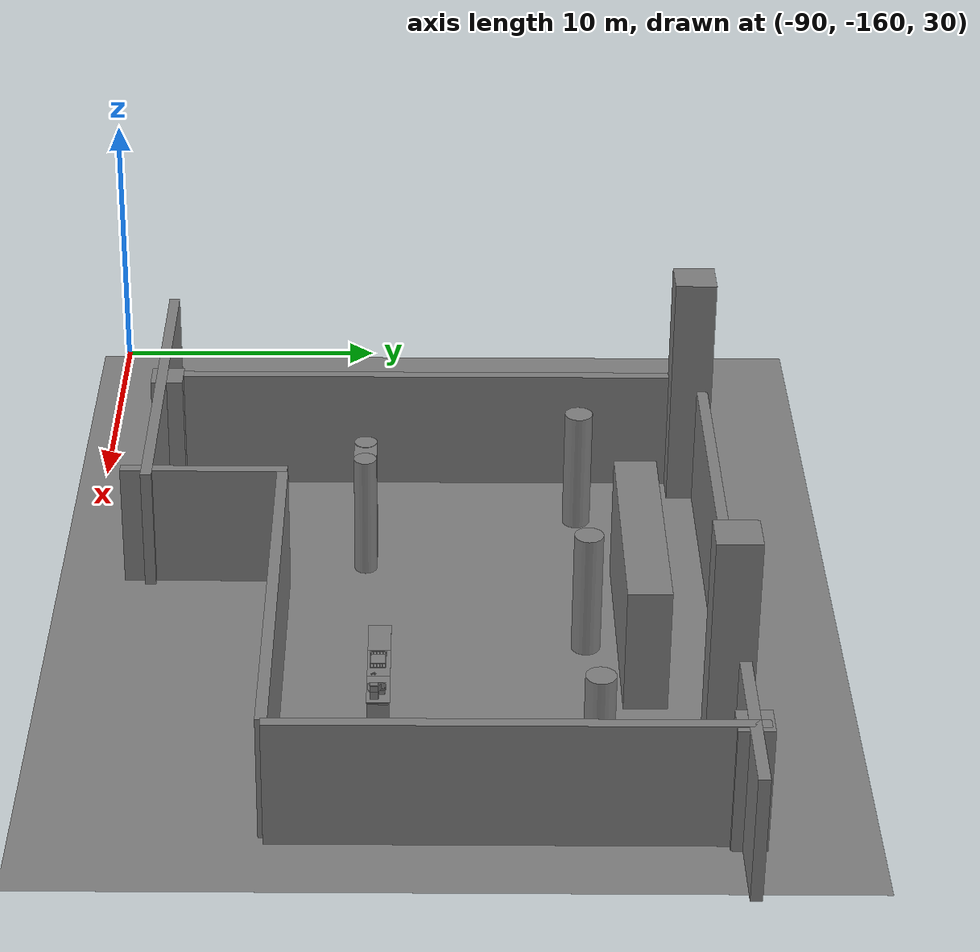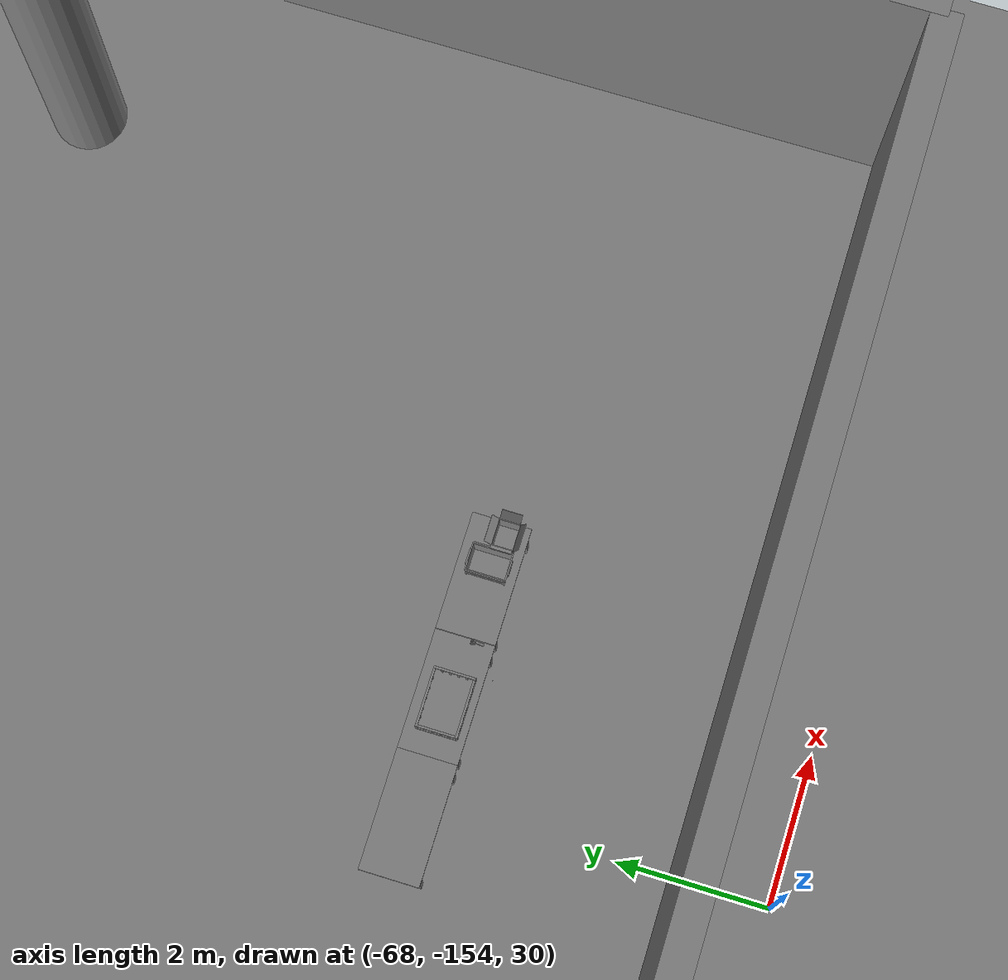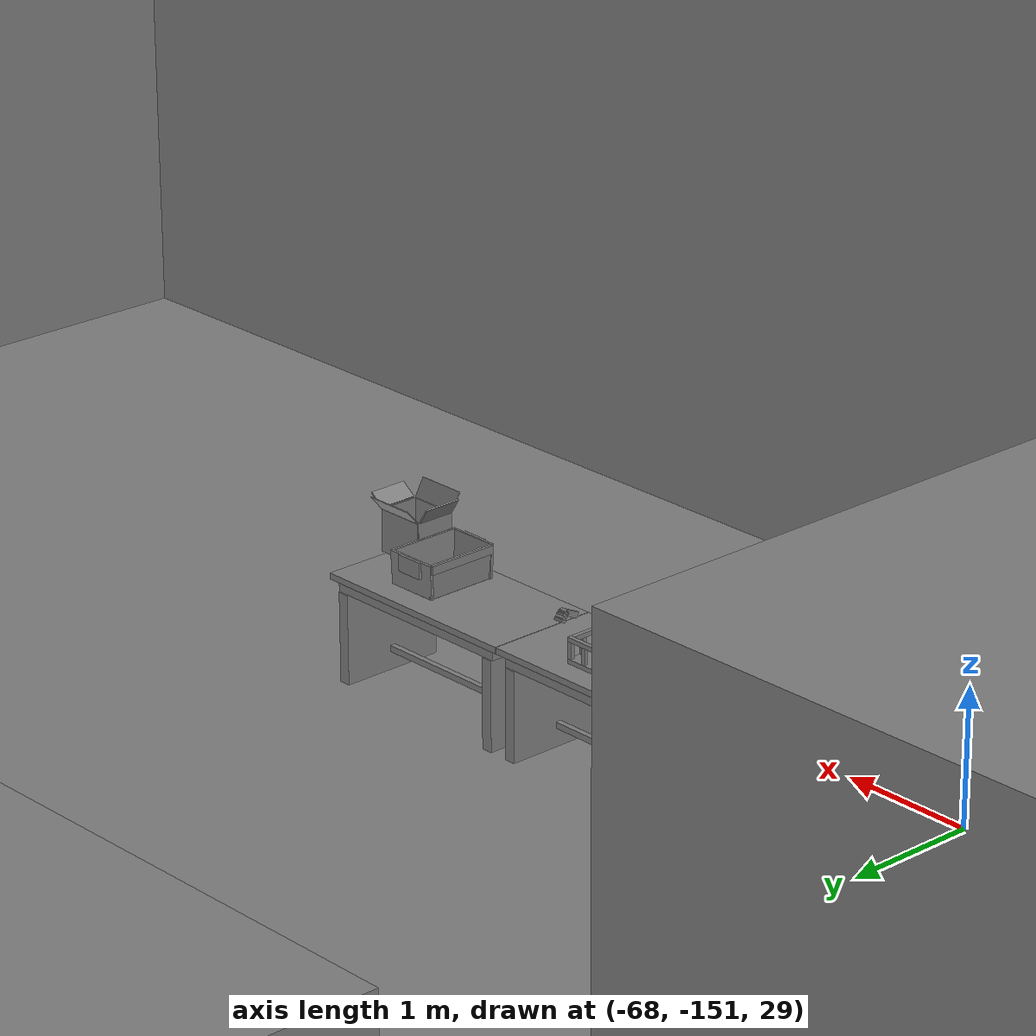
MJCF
<mujoco>
    <option gravity="0.000000000 0.000000000 -9.810000420" timestep="0.0049999999" integrator="implicitfast" density="1.225" viscosity="1.8000001e-05" noslip_iterations="10" iterations="100" sdf_iterations="50">
        <flag multiccd="disable"/>
    </option>
    <size memory="1000M"/>
    <compiler coordinate="local"/>
    <worldbody>
        <light cutoff="30" pos="0 1 1" dir="0 -1 -2"/>
        <light cutoff="30" pos="0 -1 1" dir="0 1 -2"/>
        <body pos="-64.866622925 -149.383972168 30.183746338" euler="89.999992371 89.999946594 0.000000000" name="openloong_gripper_2f85_fix_base_usda_bluebox_01">
            <geom contype="1" conaffinity="1" density="1000" type="box" material="" rgba="0.500000000 0.500000000 0.500000000 1.000000000" solimp="0.899999976 0.949999988 0.001000000" friction="1.000000000 0.005000000 0.000100000" solref="0.020000000 1.000000000" margin="0" condim="3" group="0" pos="0.276596069 0.187225342 0.000061035" quat="0.707107008 0.000077501 0.707106471 0.000077456" size="0.100000001 0.057999998 0.010000000" name="openloong_gripper_2f85_fix_base_usda_geom_0FF9C48A_197B_4F51_9246_1D325A05BD41"/>
            <geom contype="1" conaffinity="1" density="1000" type="box" material="" rgba="0.500000000 0.500000000 0.500000000 1.000000000" solimp="0.899999976 0.949999988 0.001000000" friction="1.000000000 0.005000000 0.000100000" solref="0.020000000 1.000000000" margin="0" condim="3" group="0" pos="0.000000000 0.002883911 0.000000000" quat="1.000000000 0.000000000 0.000000000 0.000000000" size="0.254000008 0.003000000 0.172000006" name="openloong_gripper_2f85_fix_base_usda_geom_E10A5166_1B41_4D81_853F_75695D272DE9"/>
            <geom contype="1" conaffinity="1" density="1000" type="box" material="" rgba="0.500000000 0.500000000 0.500000000 1.000000000" solimp="0.899999976 0.949999988 0.001000000" friction="1.000000000 0.005000000 0.000100000" solref="0.020000000 1.000000000" margin="0" condim="3" group="0" pos="0.000015259 0.124874115 0.173477173" quat="0.999796450 0.020176515 -0.000000015 0.000000030" size="0.259999990 0.119999997 0.007000000" name="openloong_gripper_2f85_fix_base_usda_geom_1E110240_6895_444E_9742_86F06F620DD1"/>
            <geom contype="1" conaffinity="1" density="1000" type="box" material="" rgba="0.500000000 0.500000000 0.500000000 1.000000000" solimp="0.899999976 0.949999988 0.001000000" friction="1.000000000 0.005000000 0.000100000" solref="0.020000000 1.000000000" margin="0" condim="3" group="0" pos="0.000015259 0.124874115 -0.173477173" quat="0.999796450 -0.020176545 -0.000000015 0.000000000" size="0.259999990 0.119999997 0.007000000" name="openloong_gripper_2f85_fix_base_usda_geom_EB683E9D_2320_457C_843A_17A9725569DD"/>
            <geom contype="1" conaffinity="1" density="1000" type="box" material="" rgba="0.500000000 0.500000000 0.500000000 1.000000000" solimp="0.899999976 0.949999988 0.001000000" friction="1.000000000 0.005000000 0.000100000" solref="0.020000000 1.000000000" margin="0" condim="3" group="0" pos="0.000015259 0.214012146 0.188980103" quat="0.999913096 0.013176724 0.000000015 0.000000000" size="0.259999990 0.029999999 0.012500000" name="openloong_gripper_2f85_fix_base_usda_geom_A93989A7_E68A_4455_A4EC_8168EF28E093"/>
            <geom contype="1" conaffinity="1" density="1000" type="box" material="" rgba="0.500000000 0.500000000 0.500000000 1.000000000" solimp="0.899999976 0.949999988 0.001000000" friction="1.000000000 0.005000000 0.000100000" solref="0.020000000 1.000000000" margin="0" condim="3" group="0" pos="-0.258346558 0.125289917 0.001876831" quat="0.702796996 -0.020792052 0.710783184 0.020769238" size="0.189999998 0.119999997 0.009000000" name="openloong_gripper_2f85_fix_base_usda_geom_434673EF_A7D0_48BA_9AAA_2FE13E9F99C3"/>
            <geom contype="1" conaffinity="1" density="1000" type="box" material="" rgba="0.500000000 0.500000000 0.500000000 1.000000000" solimp="0.899999976 0.949999988 0.001000000" friction="1.000000000 0.005000000 0.000100000" solref="0.020000000 1.000000000" margin="0" condim="3" group="0" pos="0.000015259 0.214012146 -0.188980103" quat="0.999913096 -0.013176769 0.000000030 0.000000015" size="0.259999990 0.029999999 0.012500000" name="openloong_gripper_2f85_fix_base_usda_geom_A95DB23E_68C7_4DB4_BF35_110D01929081"/>
            <geom contype="1" conaffinity="1" density="1000" type="box" material="" rgba="0.500000000 0.500000000 0.500000000 1.000000000" solimp="0.899999976 0.949999988 0.001000000" friction="1.000000000 0.005000000 0.000100000" solref="0.020000000 1.000000000" margin="0" condim="3" group="0" pos="-0.276596069 0.187225342 0.000061035" quat="0.707106650 0.000077441 0.707106709 0.000077456" size="0.100000001 0.057999998 0.010000000" name="openloong_gripper_2f85_fix_base_usda_geom_D967C9F9_22BE_4C19_BB2E_602796105679"/>
            <geom contype="1" conaffinity="1" density="1000" type="box" material="" rgba="0.500000000 0.500000000 0.500000000 1.000000000" solimp="0.899999976 0.949999988 0.001000000" friction="1.000000000 0.005000000 0.000100000" solref="0.020000000 1.000000000" margin="0" condim="3" group="0" pos="0.258346558 0.125289917 0.001876831" quat="0.702851534 0.018856451 0.710823834 -0.019329429" size="0.189999998 0.119999997 0.009000000" name="openloong_gripper_2f85_fix_base_usda_geom_22C06281_7915_4F4B_9998_6531D2C3FF37"/>
            <freejoint name="openloong_gripper_2f85_fix_base_usda_bluebox_01_joint"/>
            <site size="0.005000000 0.005000000 0.005000000" rgba="0.500000000 0.500000000 0.500000000 1.000000000" pos="0.000000000 0.000000000 0.000000000" quat="0.999961913 0.008726534 0.000000000 0.000000000" group="0" type="sphere" name="openloong_gripper_2f85_fix_base_usda_bluebox_01site"/>
        </body>
        <body pos="-64.496299744 -149.491867065 30.235729218" euler="0.000000000 0.000000000 89.999946594" name="openloong_gripper_2f85_fix_base_usda_cardboardbox_01">
            <geom contype="1" conaffinity="1" density="1000" type="box" material="" rgba="0.500000000 0.500000000 0.500000000 1.000000000" solimp="0.899999976 0.949999988 0.001000000" friction="1.000000000 0.005000000 0.000100000" solref="0.020000000 1.000000000" margin="0" condim="3" group="0" pos="-0.003166199 -0.004086494 0.005052090" quat="1.000000000 0.000000000 0.000000000 0.000000000" size="0.142499998 0.177500010 0.005000000" name="openloong_gripper_2f85_fix_base_usda_geom_EA7B4EAE_38BF_4119_8CA5_7AAD5D4D4C27"/>
            <geom contype="1" conaffinity="1" density="1000" type="box" material="" rgba="0.500000000 0.500000000 0.500000000 1.000000000" solimp="0.899999976 0.949999988 0.001000000" friction="1.000000000 0.005000000 0.000100000" solref="0.020000000 1.000000000" margin="0" condim="3" group="0" pos="-0.003166199 0.170316696 0.150570869" quat="1.000000000 0.000000000 0.000000000 0.000000000" size="0.142499998 0.005000000 0.149999991" name="openloong_gripper_2f85_fix_base_usda_geom_80D01A20_9DD7_4476_929F_074B0D558EE7"/>
            <geom contype="1" conaffinity="1" density="1000" type="box" material="" rgba="0.500000000 0.500000000 0.500000000 1.000000000" solimp="0.899999976 0.949999988 0.001000000" friction="1.000000000 0.005000000 0.000100000" solref="0.020000000 1.000000000" margin="0" condim="3" group="0" pos="-0.147399902 -0.005307198 0.150570869" quat="1.000000000 0.000000000 0.000000000 0.000000000" size="0.005000000 0.177500010 0.149999991" name="openloong_gripper_2f85_fix_base_usda_geom_9C4311CD_A5DC_414F_A79F_DEC489DCBEE7"/>
            <geom contype="1" conaffinity="1" density="1000" type="box" material="" rgba="0.500000000 0.500000000 0.500000000 1.000000000" solimp="0.899999976 0.949999988 0.001000000" friction="1.000000000 0.005000000 0.000100000" solref="0.020000000 1.000000000" margin="0" condim="3" group="0" pos="0.140275955 -0.005307198 0.150570869" quat="1.000000000 0.000000000 0.000000000 0.000000000" size="0.005000000 0.177500010 0.149999991" name="openloong_gripper_2f85_fix_base_usda_geom_6F74B92A_A441_4DC9_AE5B_F890D417F834"/>
            <geom contype="1" conaffinity="1" density="1000" type="box" material="" rgba="0.500000000 0.500000000 0.500000000 1.000000000" solimp="0.899999976 0.949999988 0.001000000" friction="1.000000000 0.005000000 0.000100000" solref="0.020000000 1.000000000" margin="0" condim="3" group="0" pos="-0.003166199 -0.181550980 0.150570869" quat="1.000000000 0.000000000 0.000000000 0.000000000" size="0.142499998 0.005000000 0.149999991" name="openloong_gripper_2f85_fix_base_usda_geom_C0C2D2C0_4520_4FE6_8B99_81CA9FA468C5"/>
            <freejoint name="openloong_gripper_2f85_fix_base_usda_cardboardbox_01_joint"/>
            <site size="0.005000000 0.005000000 0.005000000" rgba="0.500000000 0.500000000 0.500000000 1.000000000" pos="0.000000000 0.000000000 0.000000000" quat="0.999961913 0.008726535 0.000000000 0.000000000" group="0" type="sphere" name="openloong_gripper_2f85_fix_base_usda_site_58B254DE_56FD_4019_B3A4_A94779CF76C6"/>
            <body pos="0.139160156 -0.004048347 0.301930904" euler="-179.999954224 49.383502960 179.999954224" name="openloong_gripper_2f85_fix_base_usda_A1_006">
                <geom contype="1" conaffinity="1" density="1000" type="box" material="" rgba="0.500000000 0.500000000 0.500000000 1.000000000" solimp="0.899999976 0.949999988 0.001000000" friction="1.000000000 0.005000000 0.000100000" solref="0.020000000 1.000000000" margin="0" condim="3" group="0" pos="-0.071587563 0.000009537 0.001745224" quat="0.999999881 0.000000000 0.000000000 0.000000000" size="0.071249999 0.179999992 0.002500000" name="openloong_gripper_2f85_fix_base_usda_geom_8D095F6E_4BC0_4786_9A67_1818DB9696EB"/>
                <joint armature="0" stiffness="0.07" damping="0.0099999998" axis="0.000000 1.000000 0.000000" type="hinge" name="openloong_gripper_2f85_fix_base_usda_A1_006"/>
            </body>
            <body pos="-0.145902634 -0.004086494 0.301938057" euler="-180.000000000 -60.000011444 -180.000000000" name="openloong_gripper_2f85_fix_base_usda_A2_006">
                <geom contype="1" conaffinity="1" density="1000" type="box" material="" rgba="0.500000000 0.500000000 0.500000000 1.000000000" solimp="0.899999976 0.949999988 0.001000000" friction="1.000000000 0.005000000 0.000100000" solref="0.020000000 1.000000000" margin="0" condim="3" group="0" pos="0.071268082 0.000009537 0.002717972" quat="0.000002921 0.000000000 -0.000000030 0.999999881" size="0.071249999 0.179999992 0.002500000" name="openloong_gripper_2f85_fix_base_usda_geom_D8AC8B4A_54BE_4489_A251_9CB680570854"/>
                <joint armature="0" stiffness="0.07" damping="0.0099999998" axis="0.000000 1.000000 0.000000" type="hinge" name="openloong_gripper_2f85_fix_base_usda_A2_006"/>
            </body>
            <body pos="-0.003385544 0.175991058 0.301930904" euler="-125.858116150 -0.000004561 0.000002331" name="openloong_gripper_2f85_fix_base_usda_B2_006">
                <geom contype="1" conaffinity="1" density="1000" type="box" material="" rgba="0.500000000 0.500000000 0.500000000 1.000000000" solimp="0.899999976 0.949999988 0.001000000" friction="1.000000000 0.005000000 0.000100000" solref="0.020000000 1.000000000" margin="0" condim="3" group="0" pos="0.000009537 -0.070939064 -0.002470016" quat="0.999614120 0.027776197 -0.000000015 0.000000030" size="0.137500003 0.064999998 0.005000000" name="openloong_gripper_2f85_fix_base_usda_geom_395F8845_38F1_4FA2_9CD9_61BDA7A284E7"/>
                <joint armature="0" stiffness="0.07" damping="0.0099999998" axis="1.000000 0.000000 0.000000" type="hinge" name="openloong_gripper_2f85_fix_base_usda_B2_006"/>
            </body>
            <body pos="-0.003385544 -0.184140205 0.301938057" euler="147.805557251 0.000000000 0.000000000" name="openloong_gripper_2f85_fix_base_usda_B1_006">
                <geom contype="1" conaffinity="1" density="1000" type="box" material="" rgba="0.500000000 0.500000000 0.500000000 1.000000000" solimp="0.899999976 0.949999988 0.001000000" friction="1.000000000 0.005000000 0.000100000" solref="0.020000000 1.000000000" margin="0" condim="3" group="0" pos="-0.000028610 0.070202351 -0.002703667" quat="0.999614179 -0.027776167 0.000000000 0.000000000" size="0.137500003 0.064999998 0.005000000" name="openloong_gripper_2f85_fix_base_usda_geom_7361C98C_E011_4422_83BE_BA616A5A1E71"/>
                <joint armature="0" stiffness="0.07" damping="0.0099999998" axis="1.000000 0.000000 0.000000" type="hinge" name="openloong_gripper_2f85_fix_base_usda_B1_006"/>
            </body>
        </body>
        <body pos="-65.882858276 -149.481979370 30.229999542" euler="-64.487716675 0.000000000 0.000000000" name="openloong_gripper_2f85_fix_base_usda_Barcode">
            <geom contype="1" conaffinity="1" density="1000" type="box" material="" rgba="0.500000000 0.500000000 0.500000000 1.000000000" solimp="0.899999976 0.949999988 0.001000000" friction="1.000000000 0.005000000 0.000100000" solref="0.020000000 1.000000000" margin="0" condim="3" group="0" pos="0.000000000 0.013038635 0.001419067" quat="0.000000000 0.000000000 0.000000000 1.000000119" size="0.034000002 0.010000000 0.017999999" name="openloong_gripper_2f85_fix_base_usda_geom_0A297944_E22E_480A_B996_23355AE33A61"/>
            <geom contype="1" conaffinity="1" density="1000" type="box" material="" rgba="0.500000000 0.500000000 0.500000000 1.000000000" solimp="0.899999976 0.949999988 0.001000000" friction="1.000000000 0.005000000 0.000100000" solref="0.020000000 1.000000000" margin="0" condim="3" group="0" pos="0.000000000 -0.035301208 -0.007095337" quat="0.000000000 0.000000000 -0.043619365 0.999048233" size="0.028999999 0.010000000 0.020000000" name="openloong_gripper_2f85_fix_base_usda_geom_104FBE9F_D189_472A_B19B_CC56EB43DF9F"/>
            <geom contype="1" conaffinity="1" density="1000" type="box" material="" rgba="0.500000000 0.500000000 0.500000000 1.000000000" solimp="0.899999976 0.949999988 0.001000000" friction="1.000000000 0.005000000 0.000100000" solref="0.020000000 1.000000000" margin="0" condim="3" group="0" pos="0.000000000 -0.043411255 -0.011749268" quat="0.922262907 0.386563420 0.000000000 0.000000000" size="0.026000001 0.010000000 0.020000000" name="openloong_gripper_2f85_fix_base_usda_geom_725F2189_7C7C_47CF_BAE3_02E53A52FC22"/>
            <geom contype="1" conaffinity="1" density="1000" type="box" material="" rgba="0.500000000 0.500000000 0.500000000 1.000000000" solimp="0.899999976 0.949999988 0.001000000" friction="1.000000000 0.005000000 0.000100000" solref="0.020000000 1.000000000" margin="0" condim="3" group="0" pos="0.000000000 -0.016967773 -0.031860352" quat="0.000000000 0.000000000 0.000000000 1.000000119" size="0.008000000 0.010000000 0.013000000" name="openloong_gripper_2f85_fix_base_usda_geom_146201F4_3DF0_4844_BB53_C3A4F494B52E"/>
            <geom contype="1" conaffinity="1" density="1000" type="box" material="" rgba="0.500000000 0.500000000 0.500000000 1.000000000" solimp="0.899999976 0.949999988 0.001000000" friction="1.000000000 0.005000000 0.000100000" solref="0.020000000 1.000000000" margin="0" condim="3" group="0" pos="0.000000000 -0.001869202 0.000312805" quat="0.953716993 0.300705761 0.000000000 0.000000000" size="0.032000002 0.010000000 0.018999999" name="openloong_gripper_2f85_fix_base_usda_geom_1E1AE2A9_DF13_4F9E_9950_8BA3C0C625A5"/>
            <geom contype="1" conaffinity="1" density="1000" type="box" material="" rgba="0.500000000 0.500000000 0.500000000 1.000000000" solimp="0.899999976 0.949999988 0.001000000" friction="1.000000000 0.005000000 0.000100000" solref="0.020000000 1.000000000" margin="0" condim="3" group="0" pos="0.000000000 -0.019531250 -0.003173828" quat="0.953716993 0.300705761 0.000000000 0.000000000" size="0.030999999 0.010000000 0.020000000" name="openloong_gripper_2f85_fix_base_usda_geom_F75D8745_35BD_45CE_B5C4_7C214CBD5A10"/>
            <geom contype="1" conaffinity="1" density="1000" type="box" material="" rgba="0.500000000 0.500000000 0.500000000 1.000000000" solimp="0.899999976 0.949999988 0.001000000" friction="1.000000000 0.005000000 0.000100000" solref="0.020000000 1.000000000" margin="0" condim="3" group="0" pos="0.000000000 -0.035301208 -0.007095337" quat="0.953716993 0.300705761 0.000000000 0.000000000" size="0.028999999 0.010000000 0.020000000" name="openloong_gripper_2f85_fix_base_usda_geom_C5E8BD34_5123_4A4C_A8BE_D713AC86C3B1"/>
            <geom contype="1" conaffinity="1" density="1000" type="box" material="" rgba="0.500000000 0.500000000 0.500000000 1.000000000" solimp="0.899999976 0.949999988 0.001000000" friction="1.000000000 0.005000000 0.000100000" solref="0.020000000 1.000000000" margin="0" condim="3" group="0" pos="0.000000000 -0.042617798 -0.071121216" quat="0.000000000 0.000000000 0.000000000 1.000000119" size="0.013000000 0.021000000 0.059999999" name="openloong_gripper_2f85_fix_base_usda_geom_D1E18107_4B1A_4EE3_9F29_BC2FA11FBF32"/>
            <freejoint name="openloong_gripper_2f85_fix_base_usda_Barcode_joint"/>
            <site size="0.005000000 0.005000000 0.005000000" rgba="0.500000000 0.500000000 0.500000000 1.000000000" pos="0.000000000 0.000000000 0.000000000" quat="1.000000000 0.000000000 0.000000000 0.000000000" group="0" type="sphere" name="openloong_gripper_2f85_fix_base_usda_Barcode_site"/>
        </body>
        <body pos="-66.745018005 -149.392349243 30.184000015" euler="0.000000000 0.000000000 89.999946594" name="[22331213062734]_Basket_01">
            <geom contype="1" conaffinity="1" density="1000" type="box" material="" rgba="0.500000000 0.500000000 0.500000000 1.000000000" solimp="0.899999976 0.949999988 0.001000000" friction="1.000000000 0.005000000 0.000100000" solref="0.020000000 1.000000000" margin="0" condim="3" group="0" pos="-0.052425385 0.389207840 0.089787483" quat="0.707107008 0.000000000 0.000000000 0.707106411" size="0.014249999 0.014249999 0.059999999" name="[22331213062734]_geom_3B5F9D99_3FC0_425D_8D78_3D427D59542A"/>
            <geom contype="1" conaffinity="1" density="1000" type="box" material="" rgba="0.500000000 0.500000000 0.500000000 1.000000000" solimp="0.899999976 0.949999988 0.001000000" friction="1.000000000 0.005000000 0.000100000" solref="0.020000000 1.000000000" margin="0" condim="3" group="0" pos="0.264015198 -0.133043289 0.089787483" quat="0.707107008 0.000000000 0.000000000 0.707106411" size="0.014249999 0.014249999 0.059999999" name="[22331213062734]_geom_CF5726B0_2867_4A3D_B22D_92BEB14C5605"/>
            <geom contype="1" conaffinity="1" density="1000" type="box" material="" rgba="0.500000000 0.500000000 0.500000000 1.000000000" solimp="0.899999976 0.949999988 0.001000000" friction="1.000000000 0.005000000 0.000100000" solref="0.020000000 1.000000000" margin="0" condim="3" group="0" pos="-0.264015198 -0.265548706 0.089793205" quat="0.707107008 0.000000000 0.000000000 0.707106411" size="0.014249999 0.014249999 0.059999999" name="[22331213062734]_geom_ECAA93A0_AE77_4E09_929C_A2BB9D509742"/>
            <geom contype="1" conaffinity="1" density="1000" type="box" material="" rgba="0.500000000 0.500000000 0.500000000 1.000000000" solimp="0.899999976 0.949999988 0.001000000" friction="1.000000000 0.005000000 0.000100000" solref="0.020000000 1.000000000" margin="0" condim="3" group="0" pos="-0.160263062 -0.389322281 0.089793205" quat="0.707107008 0.000000000 0.000000000 0.707106411" size="0.014249999 0.014249999 0.059999999" name="[22331213062734]_geom_62A8232D_8D8B_4867_AD58_39DF8F65E698"/>
            <geom contype="1" conaffinity="1" density="1000" type="box" material="" rgba="0.500000000 0.500000000 0.500000000 1.000000000" solimp="0.899999976 0.949999988 0.001000000" friction="1.000000000 0.005000000 0.000100000" solref="0.020000000 1.000000000" margin="0" condim="3" group="0" pos="0.162265778 -0.389322281 0.089787483" quat="0.707107008 0.000000000 0.000000000 0.707106411" size="0.014249999 0.014249999 0.059999999" name="[22331213062734]_geom_1560ED24_DD6F_4A2D_B572_23B626578E9F"/>
            <geom contype="1" conaffinity="1" density="1000" type="box" material="" rgba="0.500000000 0.500000000 0.500000000 1.000000000" solimp="0.899999976 0.949999988 0.001000000" friction="1.000000000 0.005000000 0.000100000" solref="0.020000000 1.000000000" margin="0" condim="3" group="0" pos="0.264015198 0.389207840 0.089787483" quat="0.707107008 0.000000000 0.000000000 0.707106411" size="0.014249999 0.014249999 0.059999999" name="[22331213062734]_geom_A59AC13E_F971_485B_86C7_F31D6BD16B56"/>
            <geom contype="1" conaffinity="1" density="1000" type="box" material="" rgba="0.500000000 0.500000000 0.500000000 1.000000000" solimp="0.899999976 0.949999988 0.001000000" friction="1.000000000 0.005000000 0.000100000" solref="0.020000000 1.000000000" margin="0" condim="3" group="0" pos="-0.264015198 -0.133043289 0.089793205" quat="0.707107008 0.000000000 0.000000000 0.707106411" size="0.014249999 0.014249999 0.059999999" name="[22331213062734]_geom_165AB18D_2FDD_4110_B168_93263CFB914A"/>
            <geom contype="1" conaffinity="1" density="1000" type="box" material="" rgba="0.500000000 0.500000000 0.500000000 1.000000000" solimp="0.899999976 0.949999988 0.001000000" friction="1.000000000 0.005000000 0.000100000" solref="0.020000000 1.000000000" margin="0" condim="3" group="0" pos="-0.264026642 0.269256592 0.089793205" quat="0.707107008 0.000000000 0.000000000 0.707106411" size="0.014249999 0.014249999 0.059999999" name="[22331213062734]_geom_97108733_6019_4E31_8506_49132A502613"/>
            <geom contype="1" conaffinity="1" density="1000" type="box" material="" rgba="0.500000000 0.500000000 0.500000000 1.000000000" solimp="0.899999976 0.949999988 0.001000000" friction="1.000000000 0.005000000 0.000100000" solref="0.020000000 1.000000000" margin="0" condim="3" group="0" pos="0.054462433 0.389207840 0.089787483" quat="0.707107008 0.000000000 0.000000000 0.707106411" size="0.014249999 0.014249999 0.059999999" name="[22331213062734]_geom_36E3FDD7_9109_4FB8_8ADC_3E9F19699962"/>
            <geom contype="1" conaffinity="1" density="1000" type="box" material="" rgba="0.500000000 0.500000000 0.500000000 1.000000000" solimp="0.899999976 0.949999988 0.001000000" friction="1.000000000 0.005000000 0.000100000" solref="0.020000000 1.000000000" margin="0" condim="3" group="0" pos="0.054462433 -0.389322281 0.089787483" quat="0.707107008 0.000000000 0.000000000 0.707106411" size="0.014249999 0.014249999 0.059999999" name="[22331213062734]_geom_A67CB686_3DB5_49D6_9017_D72AF4A432F8"/>
            <geom contype="1" conaffinity="1" density="1000" type="box" material="" rgba="0.500000000 0.500000000 0.500000000 1.000000000" solimp="0.899999976 0.949999988 0.001000000" friction="1.000000000 0.005000000 0.000100000" solref="0.020000000 1.000000000" margin="0" condim="3" group="0" pos="0.264015198 0.269256592 0.089793205" quat="0.707107008 0.000000000 0.000000000 0.707106411" size="0.014249999 0.014249999 0.059999999" name="[22331213062734]_geom_4F79A347_6C21_4A08_85C9_7FD59C2D6808"/>
            <geom contype="1" conaffinity="1" density="1000" type="box" material="" rgba="0.500000000 0.500000000 0.500000000 1.000000000" solimp="0.899999976 0.949999988 0.001000000" friction="1.000000000 0.005000000 0.000100000" solref="0.020000000 1.000000000" margin="0" condim="3" group="0" pos="0.264015198 -0.389322281 0.089787483" quat="0.707107008 0.000000000 0.000000000 0.707106411" size="0.014249999 0.014249999 0.059999999" name="[22331213062734]_geom_532FFC08_BE36_422D_814C_6D0D802AE979"/>
            <geom contype="1" conaffinity="1" density="1000" type="box" material="" rgba="0.500000000 0.500000000 0.500000000 1.000000000" solimp="0.899999976 0.949999988 0.001000000" friction="1.000000000 0.005000000 0.000100000" solref="0.020000000 1.000000000" margin="0" condim="3" group="0" pos="0.000000000 0.000000000 0.015998840" quat="0.707107008 0.000000000 0.000000000 0.707106411" size="0.403499991 0.279000014 0.015750000" name="[22331213062734]_geom_8B8A8CD9_B8D7_48CA_A5DF_FF83542267DD"/>
            <geom contype="1" conaffinity="1" density="1000" type="box" material="" rgba="0.500000000 0.500000000 0.500000000 1.000000000" solimp="0.899999976 0.949999988 0.001000000" friction="1.000000000 0.005000000 0.000100000" solref="0.020000000 1.000000000" margin="0" condim="3" group="0" pos="0.000000000 -0.389476776 0.163619041" quat="0.707107008 0.000000000 0.000000000 0.707106411" size="0.015000000 0.277500004 0.015750000" name="[22331213062734]_geom_30FDFC8E_99D2_4630_AC9B_6B88DE451C21"/>
            <geom contype="1" conaffinity="1" density="1000" type="box" material="" rgba="0.500000000 0.500000000 0.500000000 1.000000000" solimp="0.899999976 0.949999988 0.001000000" friction="1.000000000 0.005000000 0.000100000" solref="0.020000000 1.000000000" margin="0" condim="3" group="0" pos="0.162265778 0.389207840 0.089787483" quat="0.707107008 0.000000000 0.000000000 0.707106411" size="0.014249999 0.014249999 0.059999999" name="[22331213062734]_geom_F23FA48B_9724_4E2D_95D5_8DC58C0469EF"/>
            <geom contype="1" conaffinity="1" density="1000" type="box" material="" rgba="0.500000000 0.500000000 0.500000000 1.000000000" solimp="0.899999976 0.949999988 0.001000000" friction="1.000000000 0.005000000 0.000100000" solref="0.020000000 1.000000000" margin="0" condim="3" group="0" pos="0.000000000 0.389471054 0.163619041" quat="0.707107008 0.000000000 0.000000000 0.707106411" size="0.015000000 0.277500004 0.015750000" name="[22331213062734]_geom_9B52D01C_D876_4B8D_8E65_D3873247FBC9"/>
            <geom contype="1" conaffinity="1" density="1000" type="box" material="" rgba="0.500000000 0.500000000 0.500000000 1.000000000" solimp="0.899999976 0.949999988 0.001000000" friction="1.000000000 0.005000000 0.000100000" solref="0.020000000 1.000000000" margin="0" condim="3" group="0" pos="-0.263511658 0.000000000 0.163619041" quat="0.707107008 0.000000000 0.000000000 0.707106411" size="0.403499991 0.015000000 0.015750000" name="[22331213062734]_geom_53BC78EE_D6D6_4F68_91AD_BA5178AD89DC"/>
            <geom contype="1" conaffinity="1" density="1000" type="box" material="" rgba="0.500000000 0.500000000 0.500000000 1.000000000" solimp="0.899999976 0.949999988 0.001000000" friction="1.000000000 0.005000000 0.000100000" solref="0.020000000 1.000000000" margin="0" condim="3" group="0" pos="-0.264015198 0.141334534 0.089793205" quat="0.707107008 0.000000000 0.000000000 0.707106411" size="0.014249999 0.014249999 0.059999999" name="[22331213062734]_geom_97B589F8_D8F5_4F2F_803A_38CFA6B04DA4"/>
            <geom contype="1" conaffinity="1" density="1000" type="box" material="" rgba="0.500000000 0.500000000 0.500000000 1.000000000" solimp="0.899999976 0.949999988 0.001000000" friction="1.000000000 0.005000000 0.000100000" solref="0.020000000 1.000000000" margin="0" condim="3" group="0" pos="0.264015198 -0.265548706 0.089787483" quat="0.707107008 0.000000000 0.000000000 0.707106411" size="0.014249999 0.014249999 0.059999999" name="[22331213062734]_geom_5AE1EAC9_D9E3_476E_9AAB_A7E5DDEE17B8"/>
            <geom contype="1" conaffinity="1" density="1000" type="box" material="" rgba="0.500000000 0.500000000 0.500000000 1.000000000" solimp="0.899999976 0.949999988 0.001000000" friction="1.000000000 0.005000000 0.000100000" solref="0.020000000 1.000000000" margin="0" condim="3" group="0" pos="-0.160263062 0.389207840 0.089787483" quat="0.707107008 0.000000000 0.000000000 0.707106411" size="0.014249999 0.014249999 0.059999999" name="[22331213062734]_geom_30E8B7F3_74A0_409B_8575_AD90D58317BB"/>
            <geom contype="1" conaffinity="1" density="1000" type="box" material="" rgba="0.500000000 0.500000000 0.500000000 1.000000000" solimp="0.899999976 0.949999988 0.001000000" friction="1.000000000 0.005000000 0.000100000" solref="0.020000000 1.000000000" margin="0" condim="3" group="0" pos="-0.052425385 -0.389322281 0.089787483" quat="0.707107008 0.000000000 0.000000000 0.707106411" size="0.014249999 0.014249999 0.059999999" name="[22331213062734]_geom_B52A6B81_8DBF_4EC5_A674_626266D0CD55"/>
            <geom contype="1" conaffinity="1" density="1000" type="box" material="" rgba="0.500000000 0.500000000 0.500000000 1.000000000" solimp="0.899999976 0.949999988 0.001000000" friction="1.000000000 0.005000000 0.000100000" solref="0.020000000 1.000000000" margin="0" condim="3" group="0" pos="-0.264026642 -0.389322281 0.089793205" quat="0.707107008 0.000000000 0.000000000 0.707106411" size="0.014249999 0.014249999 0.059999999" name="[22331213062734]_geom_45CDD3C8_E698_458C_BF01_A0DFBE239537"/>
            <geom contype="1" conaffinity="1" density="1000" type="box" material="" rgba="0.500000000 0.500000000 0.500000000 1.000000000" solimp="0.899999976 0.949999988 0.001000000" friction="1.000000000 0.005000000 0.000100000" solref="0.020000000 1.000000000" margin="0" condim="3" group="0" pos="0.264015198 0.141334534 0.089787483" quat="0.707107008 0.000000000 0.000000000 0.707106411" size="0.014249999 0.014249999 0.059999999" name="[22331213062734]_geom_FBA2EA8B_8658_48EF_ACD1_1D52350C521A"/>
            <geom contype="1" conaffinity="1" density="1000" type="box" material="" rgba="0.500000000 0.500000000 0.500000000 1.000000000" solimp="0.899999976 0.949999988 0.001000000" friction="1.000000000 0.005000000 0.000100000" solref="0.020000000 1.000000000" margin="0" condim="3" group="0" pos="-0.264015198 0.389207840 0.089793205" quat="0.707107008 0.000000000 0.000000000 0.707106411" size="0.014249999 0.014249999 0.059999999" name="[22331213062734]_geom_F1375E4F_D8B5_4853_97FF_7A04B640DC12"/>
            <geom contype="1" conaffinity="1" density="1000" type="box" material="" rgba="0.500000000 0.500000000 0.500000000 1.000000000" solimp="0.899999976 0.949999988 0.001000000" friction="1.000000000 0.005000000 0.000100000" solref="0.020000000 1.000000000" margin="0" condim="3" group="0" pos="0.264015198 0.004480362 0.089787483" quat="0.707107008 0.000000000 0.000000000 0.707106411" size="0.014249999 0.014249999 0.059999999" name="[22331213062734]_geom_9BE603D7_3A03_4E03_A406_EF4BDCAF317C"/>
            <geom contype="1" conaffinity="1" density="1000" type="box" material="" rgba="0.500000000 0.500000000 0.500000000 1.000000000" solimp="0.899999976 0.949999988 0.001000000" friction="1.000000000 0.005000000 0.000100000" solref="0.020000000 1.000000000" margin="0" condim="3" group="0" pos="0.263694763 -0.000011444 0.163619041" quat="0.707107008 0.000000000 0.000000000 0.707106411" size="0.403499991 0.015000000 0.015750000" name="[22331213062734]_geom_5A771EC0_EC97_410A_A99E_B7CC7A5173BB"/>
            <geom contype="1" conaffinity="1" density="1000" type="box" material="" rgba="0.500000000 0.500000000 0.500000000 1.000000000" solimp="0.899999976 0.949999988 0.001000000" friction="1.000000000 0.005000000 0.000100000" solref="0.020000000 1.000000000" margin="0" condim="3" group="0" pos="-0.264015198 0.004480362 0.089793205" quat="0.707107008 0.000000000 0.000000000 0.707106411" size="0.014249999 0.014249999 0.059999999" name="[22331213062734]_geom_597BE8E7_859E_4251_97E4_E15A0E22A77C"/>
            <freejoint name="[22331213062734]_joint_AFEC5C8E_DCD3_44F8_9A1D_F5DE245F07C5"/>
        </body>
        <body pos="0.000000000 0.000000000 0.000000000" euler="0.000000000 0.000000000 0.000000000" name="Static Objects_Static Objects">
            <geom contype="1" conaffinity="1" density="1000" type="box" material="" rgba="0.500000000 0.500000000 0.500000000 1.000000000" solimp="0.899999976 0.949999988 0.001000000" friction="1.000000000 0.005000000 0.000100000" solref="0.020000000 1.000000000" margin="0" condim="3" group="0" pos="-67.544113159 -149.365814209 29.727830887" quat="0.500000417 0.499999970 0.499999553 0.499999970" size="0.381000012 0.319999993 0.041000001" name="Static Objects_geom_B3CAAF76_A355_480B_B36D_FF21E91A4E80"/>
            <geom contype="1" conaffinity="1" density="1000" type="box" material="" rgba="0.500000000 0.500000000 0.500000000 1.000000000" solimp="0.899999976 0.949999988 0.001000000" friction="1.000000000 0.005000000 0.000100000" solref="0.020000000 1.000000000" margin="0" condim="3" group="0" pos="-68.239501953 -149.365814209 30.086868286" quat="0.500000417 0.499999970 0.499999553 0.499999970" size="0.370999992 0.039500002 0.745000005" name="Static Objects_geom_E404D65C_A48B_41CF_A1BA_765555FFDBDD"/>
            <geom contype="1" conaffinity="1" density="1000" type="box" material="" rgba="0.500000000 0.500000000 0.500000000 1.000000000" solimp="0.899999976 0.949999988 0.001000000" friction="1.000000000 0.005000000 0.000100000" solref="0.020000000 1.000000000" margin="0" condim="3" group="0" pos="-68.239501953 -149.365814209 30.147235870" quat="0.500000417 0.499999970 0.499999553 0.499999970" size="0.400000006 0.022000000 0.800000012" name="Static Objects_geom_208D67DE_D0F9_472E_A83C_FD06BFF5D908"/>
            <geom contype="1" conaffinity="1" density="1000" type="box" material="" rgba="0.500000000 0.500000000 0.500000000 1.000000000" solimp="0.899999976 0.949999988 0.001000000" friction="1.000000000 0.005000000 0.000100000" solref="0.020000000 1.000000000" margin="0" condim="3" group="0" pos="-68.934890747 -149.365814209 29.727830887" quat="0.500000417 0.499999970 0.499999553 0.499999970" size="0.381000012 0.319999993 0.041000001" name="Static Objects_geom_42E33E1A_025F_4D52_819E_3D76AE387C58"/>
            <geom contype="1" conaffinity="1" density="1000" type="box" material="" rgba="0.500000000 0.500000000 0.500000000 1.000000000" solimp="0.899999976 0.949999988 0.001000000" friction="1.000000000 0.005000000 0.000100000" solref="0.020000000 1.000000000" margin="0" condim="3" group="0" pos="-68.239501953 -149.365814209 29.561563492" quat="0.500000417 0.499999970 0.499999553 0.499999970" size="0.020000000 0.022000000 0.660000026" name="Static Objects_geom_08DDADE9_45CD_465D_96BC_9F4486B3209D"/>
            <geom contype="1" conaffinity="1" density="1000" type="box" material="" rgba="0.500000000 0.500000000 0.500000000 1.000000000" solimp="0.899999976 0.949999988 0.001000000" friction="1.000000000 0.005000000 0.000100000" solref="0.020000000 1.000000000" margin="0" condim="3" group="0" pos="-65.945671082 -149.365814209 29.727830887" quat="0.500000417 0.499999970 0.499999553 0.499999970" size="0.381000012 0.319999993 0.041000001" name="Static Objects_geom_445B6D14_1988_453D_A081_91407C6DB8E0"/>
            <geom contype="1" conaffinity="1" density="1000" type="box" material="" rgba="0.500000000 0.500000000 0.500000000 1.000000000" solimp="0.899999976 0.949999988 0.001000000" friction="1.000000000 0.005000000 0.000100000" solref="0.020000000 1.000000000" margin="0" condim="3" group="0" pos="-66.641059875 -149.365814209 30.086868286" quat="0.500000417 0.499999970 0.499999553 0.499999970" size="0.370999992 0.039500002 0.745000005" name="Static Objects_geom_D7D6C675_52D2_44D4_8EDA_A15147973E92"/>
            <geom contype="1" conaffinity="1" density="1000" type="box" material="" rgba="0.500000000 0.500000000 0.500000000 1.000000000" solimp="0.899999976 0.949999988 0.001000000" friction="1.000000000 0.005000000 0.000100000" solref="0.020000000 1.000000000" margin="0" condim="3" group="0" pos="-66.641059875 -149.365814209 30.147235870" quat="0.500000417 0.499999970 0.499999553 0.499999970" size="0.400000006 0.022000000 0.800000012" name="Static Objects_geom_485923A0_C1CA_4588_9CB1_0934F62E6BFB"/>
            <geom contype="1" conaffinity="1" density="1000" type="box" material="" rgba="0.500000000 0.500000000 0.500000000 1.000000000" solimp="0.899999976 0.949999988 0.001000000" friction="1.000000000 0.005000000 0.000100000" solref="0.020000000 1.000000000" margin="0" condim="3" group="0" pos="-67.336448669 -149.365814209 29.727830887" quat="0.500000417 0.499999970 0.499999553 0.499999970" size="0.381000012 0.319999993 0.041000001" name="Static Objects_geom_B1E541CD_C0AA_4520_907E_0E7D072D1795"/>
            <geom contype="1" conaffinity="1" density="1000" type="box" material="" rgba="0.500000000 0.500000000 0.500000000 1.000000000" solimp="0.899999976 0.949999988 0.001000000" friction="1.000000000 0.005000000 0.000100000" solref="0.020000000 1.000000000" margin="0" condim="3" group="0" pos="-66.641059875 -149.365814209 29.561563492" quat="0.500000417 0.499999970 0.499999553 0.499999970" size="0.020000000 0.022000000 0.660000026" name="Static Objects_geom_453240EA_728F_432D_A417_1669E66A1CAB"/>
            <geom contype="1" conaffinity="1" density="1000" type="box" material="" rgba="0.500000000 0.500000000 0.500000000 1.000000000" solimp="0.899999976 0.949999988 0.001000000" friction="1.000000000 0.005000000 0.000100000" solref="0.020000000 1.000000000" margin="0" condim="3" group="0" pos="-64.338577271 -149.365814209 29.727830887" quat="0.500000417 0.499999970 0.499999553 0.499999970" size="0.381000012 0.319999993 0.041000001" name="Static Objects_geom_26C5D5FC_BB21_43FF_961E_5AA2065ABF56"/>
            <geom contype="1" conaffinity="1" density="1000" type="box" material="" rgba="0.500000000 0.500000000 0.500000000 1.000000000" solimp="0.899999976 0.949999988 0.001000000" friction="1.000000000 0.005000000 0.000100000" solref="0.020000000 1.000000000" margin="0" condim="3" group="0" pos="-65.033966064 -149.365814209 30.086868286" quat="0.500000417 0.499999970 0.499999553 0.499999970" size="0.370999992 0.039500002 0.745000005" name="Static Objects_geom_772D1498_5BFC_4006_A4A5_92B22C6E0A63"/>
            <geom contype="1" conaffinity="1" density="1000" type="box" material="" rgba="0.500000000 0.500000000 0.500000000 1.000000000" solimp="0.899999976 0.949999988 0.001000000" friction="1.000000000 0.005000000 0.000100000" solref="0.020000000 1.000000000" margin="0" condim="3" group="0" pos="-65.033966064 -149.365814209 30.147235870" quat="0.500000417 0.499999970 0.499999553 0.499999970" size="0.400000006 0.022000000 0.800000012" name="Static Objects_geom_6B3443A7_132B_4A48_A285_345F7F1D73F4"/>
            <geom contype="1" conaffinity="1" density="1000" type="box" material="" rgba="0.500000000 0.500000000 0.500000000 1.000000000" solimp="0.899999976 0.949999988 0.001000000" friction="1.000000000 0.005000000 0.000100000" solref="0.020000000 1.000000000" margin="0" condim="3" group="0" pos="-65.729354858 -149.365814209 29.727830887" quat="0.500000417 0.499999970 0.499999553 0.499999970" size="0.381000012 0.319999993 0.041000001" name="Static Objects_geom_091C3B7B_6676_431E_B419_D63A5DA68E97"/>
            <geom contype="1" conaffinity="1" density="1000" type="box" material="" rgba="0.500000000 0.500000000 0.500000000 1.000000000" solimp="0.899999976 0.949999988 0.001000000" friction="1.000000000 0.005000000 0.000100000" solref="0.020000000 1.000000000" margin="0" condim="3" group="0" pos="-65.033966064 -149.365814209 29.561563492" quat="0.500000417 0.499999970 0.499999553 0.499999970" size="0.020000000 0.022000000 0.660000026" name="Static Objects_geom_7BCB5F28_F1FB_4156_8C39_7EFEF0B23661"/>
            <geom contype="1" conaffinity="1" density="1000" type="box" material="" rgba="0.500000000 0.500000000 0.500000000 1.000000000" solimp="0.899999976 0.949999988 0.001000000" friction="1.000000000 0.005000000 0.000100000" solref="0.020000000 1.000000000" margin="0" condim="3" group="0" pos="-61.754566193 -137.853729248 33.906845093" quat="0.707107067 0.000000000 0.000000000 0.707106471" size="0.759999990 0.759999990 4.500000000" name="Static Objects_geom_58036064_DB54_4292_8657_66F95E574E85"/>
            <geom contype="1" conaffinity="1" density="1000" type="box" material="" rgba="0.500000000 0.500000000 0.500000000 1.000000000" solimp="0.899999976 0.949999988 0.001000000" friction="1.000000000 0.005000000 0.000100000" solref="0.020000000 1.000000000" margin="0" condim="3" group="0" pos="-57.511135101 -144.927108765 31.707921982" quat="1.000000000 0.000000000 0.000000000 0.000000000" size="0.200000003 8.000000000 2.299999952" name="Static Objects_geom_C912506D_4509_4B3F_AB6B_C3A7985531B6"/>
            <geom contype="1" conaffinity="1" density="1000" type="box" material="" rgba="0.500000000 0.500000000 0.500000000 1.000000000" solimp="0.899999976 0.949999988 0.001000000" friction="1.000000000 0.005000000 0.000100000" solref="0.020000000 1.000000000" margin="0" condim="3" group="0" pos="-80.517646790 -157.574050903 31.688196182" quat="0.707107067 0.000000000 0.000000000 0.707106471" size="0.600000024 0.600000024 2.299999952" name="Static Objects_geom_3165ED8A_D936_4CC2_9662_8BC5EFB3ED8A"/>
            <geom contype="1" conaffinity="1" density="1000" type="box" material="" rgba="0.500000000 0.500000000 0.500000000 1.000000000" solimp="0.899999976 0.949999988 0.001000000" friction="1.000000000 0.005000000 0.000100000" solref="0.020000000 1.000000000" margin="0" condim="3" group="0" pos="-80.711044312 -147.414932251 31.666158676" quat="1.000000000 0.000000000 0.000000000 0.000000000" size="0.200000003 10.000000000 2.299999952" name="Static Objects_geom_654EEEF9_E7B8_40A0_B712_DCAAC7EBEC1A"/>
            <geom contype="1" conaffinity="1" density="1000" type="box" material="" rgba="0.500000000 0.500000000 0.500000000 1.000000000" solimp="0.899999976 0.949999988 0.001000000" friction="1.000000000 0.005000000 0.000100000" solref="0.020000000 1.000000000" margin="0" condim="3" group="0" pos="-57.687217712 -137.434692383 31.688196182" quat="0.707107067 0.000000000 0.000000000 0.707106471" size="0.600000024 0.600000024 2.299999952" name="Static Objects_geom_1C8F426E_F4EE_4068_8DBD_4D463F202555"/>
            <geom contype="1" conaffinity="1" density="1000" type="box" material="" rgba="0.500000000 0.500000000 0.500000000 1.000000000" solimp="0.899999976 0.949999988 0.001000000" friction="1.000000000 0.005000000 0.000100000" solref="0.020000000 1.000000000" margin="0" condim="3" group="0" pos="-69.537033081 -140.263229370 31.714921951" quat="0.707107067 0.000000000 0.000000000 0.707106471" size="0.759999990 4.500000000 2.299999952" name="Static Objects_geom_FE4CAC59_2E39_44A6_8EB8_22937E29AC68"/>
            <geom contype="1" conaffinity="1" density="1000" type="box" material="" rgba="0.500000000 0.500000000 0.500000000 1.000000000" solimp="0.899999976 0.949999988 0.001000000" friction="1.000000000 0.005000000 0.000100000" solref="0.020000000 1.000000000" margin="0" condim="3" group="0" pos="-80.073638916 -137.853713989 33.906845093" quat="0.707107067 0.000000000 0.000000000 0.707106471" size="0.759999990 0.759999990 4.500000000" name="Static Objects_geom_7B0FCEF1_6384_4934_863C_0552D86E87F5"/>
            <geom contype="1" conaffinity="1" density="1000" type="box" material="" rgba="0.500000000 0.500000000 0.500000000 1.000000000" solimp="0.899999976 0.949999988 0.001000000" friction="1.000000000 0.005000000 0.000100000" solref="0.020000000 1.000000000" margin="0" condim="3" group="0" pos="-73.406707764 -155.734664917 31.707921982" quat="1.000000000 0.000000000 0.000000000 0.000000000" size="0.200000003 3.000000000 2.299999952" name="Static Objects_geom_4AAE12D4_55A1_448B_83A3_D3C326E2AE16"/>
            <geom contype="1" conaffinity="1" density="1000" type="box" material="" rgba="0.500000000 0.500000000 0.500000000 1.000000000" solimp="0.899999976 0.949999988 0.001000000" friction="1.000000000 0.005000000 0.000100000" solref="0.020000000 1.000000000" margin="0" condim="3" group="0" pos="-68.497543335 -137.448257446 31.707921982" quat="0.707107067 0.000000000 0.000000000 0.707106471" size="0.200000003 14.000000000 2.299999952" name="Static Objects_geom_DDF017E8_B5E0_411E_879C_F9F1933AD6A0"/>
            <geom contype="1" conaffinity="1" density="1000" type="cylinder" material="" rgba="0.500000000 0.500000000 0.500000000 1.000000000" solimp="0.899999976 0.949999988 0.001000000" friction="1.000000000 0.005000000 0.000100000" solref="0.020000000 1.000000000" margin="0" condim="3" group="0" pos="-68.868522644 -142.134506226 31.711090088" quat="0.707107067 0.000000000 0.000000000 0.707106471" size="0.509999990 2.299999952 1.000000000" name="Static Objects_geom_572CBDE4_C971_48FA_9C32_FC6C61ED27F0"/>
            <geom contype="1" conaffinity="1" density="1000" type="plane" material="" rgba="0.500000000 0.500000000 0.500000000 1.000000000" solimp="0.899999976 0.949999988 0.001000000" friction="1.000000000 0.005000000 0.000100000" solref="0.020000000 1.000000000" margin="0" condim="3" group="0" pos="-72.873703003 -147.131927490 29.409669876" quat="1.000000000 0.000000000 0.000000000 0.000000000" size="18.000000000 14.000000000 1.000000000" name="Static Objects_geom_8ED3AB7A_6871_451B_A889_72922EA90203"/>
            <geom contype="1" conaffinity="1" density="1000" type="box" material="" rgba="0.500000000 0.500000000 0.500000000 1.000000000" solimp="0.899999976 0.949999988 0.001000000" friction="1.000000000 0.005000000 0.000100000" solref="0.020000000 1.000000000" margin="0" condim="3" group="0" pos="-79.943580627 -157.782272339 31.707921982" quat="0.707107067 0.000000000 0.000000000 0.707106471" size="0.200000003 7.000000000 2.299999952" name="Static Objects_geom_AC3A5D0C_A7F4_4194_ADC5_32E0EB5CE6FA"/>
            <geom contype="1" conaffinity="1" density="1000" type="box" material="" rgba="0.500000000 0.500000000 0.500000000 1.000000000" solimp="0.899999976 0.949999988 0.001000000" friction="1.000000000 0.005000000 0.000100000" solref="0.020000000 1.000000000" margin="0" condim="3" group="0" pos="-65.421028137 -152.903442383 31.707921982" quat="0.707107067 0.000000000 0.000000000 0.707106471" size="0.200000003 7.800000191 2.299999952" name="Static Objects_geom_50314737_1000_45CA_9341_5B5C47E3904C"/>
            <geom contype="1" conaffinity="1" density="1000" type="box" material="" rgba="0.500000000 0.500000000 0.500000000 1.000000000" solimp="0.899999976 0.949999988 0.001000000" friction="1.000000000 0.005000000 0.000100000" solref="0.020000000 1.000000000" margin="0" condim="3" group="0" pos="-74.776908875 -149.964416504 31.688196182" quat="1.000000000 0.000000000 0.000000000 0.000000000" size="0.600000024 0.409999996 2.299999952" name="Static Objects_geom_5E436607_0319_4A12_A298_8EE7C5368CCE"/>
            <geom contype="1" conaffinity="1" density="1000" type="cylinder" material="" rgba="0.500000000 0.500000000 0.500000000 1.000000000" solimp="0.899999976 0.949999988 0.001000000" friction="1.000000000 0.005000000 0.000100000" solref="0.020000000 1.000000000" margin="0" condim="3" group="0" pos="-60.161884308 -142.134506226 31.711090088" quat="0.707107067 0.000000000 0.000000000 0.707106471" size="0.509999990 2.299999952 1.000000000" name="Static Objects_geom_D8AE5621_02AC_44AB_973F_7ED3788DA571"/>
            <geom contype="1" conaffinity="1" density="1000" type="cylinder" material="" rgba="0.500000000 0.500000000 0.500000000 1.000000000" solimp="0.899999976 0.949999988 0.001000000" friction="1.000000000 0.005000000 0.000100000" solref="0.020000000 1.000000000" margin="0" condim="3" group="0" pos="-75.382453918 -149.963455200 31.711090088" quat="0.707107067 0.000000000 0.000000000 0.707106471" size="0.409999996 2.299999952 1.000000000" name="Static Objects_geom_A280AD02_D5F5_46C3_9884_02AB4F8F4B30"/>
            <geom contype="1" conaffinity="1" density="1000" type="cylinder" material="" rgba="0.500000000 0.500000000 0.500000000 1.000000000" solimp="0.899999976 0.949999988 0.001000000" friction="1.000000000 0.005000000 0.000100000" solref="0.020000000 1.000000000" margin="0" condim="3" group="0" pos="-74.154960632 -149.963455200 31.711090088" quat="0.707107067 0.000000000 0.000000000 0.707106471" size="0.409999996 2.299999952 1.000000000" name="Static Objects_geom_DE881A52_41A0_40F9_8D49_A1E1A0C6CAD6"/>
            <geom contype="1" conaffinity="1" density="1000" type="cylinder" material="" rgba="0.500000000 0.500000000 0.500000000 1.000000000" solimp="0.899999976 0.949999988 0.001000000" friction="1.000000000 0.005000000 0.000100000" solref="0.020000000 1.000000000" margin="0" condim="3" group="0" pos="-77.566612244 -142.134506226 31.711090088" quat="0.707107067 0.000000000 0.000000000 0.707106471" size="0.509999990 2.299999952 1.000000000" name="Static Objects_geom_D8082176_E50B_4E08_8E10_44BE6CF1E86C"/>
        </body>
        <body pos="-66.291030884 -149.869689941 29.018842697" euler="0.000000000 0.000000000 89.999946594" mocap="true" name="openloong_gripper_2f85_fix_base_usda_leftHandMocap"/>
        <body pos="-66.291030884 -149.869689941 29.018842697" euler="0.000000000 0.000000000 89.999946594" mocap="true" name="openloong_gripper_2f85_fix_base_usda_rightHandMocap"/>
        <body pos="-66.291030884 -149.869689941 30.218843460" euler="0.000000000 0.000000000 89.999946594" name="openloong_gripper_2f85_fix_base_usda_base_link">
            <geom contype="1" conaffinity="1" density="1000" type="mesh" material="" rgba="0.783999979 0.783999979 0.783999979 1.000000000" solimp="0.899999976 0.949999988 0.001000000" friction="1.000000000 0.005000000 0.000100000" solref="0.020000000 1.000000000" margin="0" condim="3" group="3" mesh="base_link" pos="0.000000000 0.000000000 0.000000000" quat="1.000000000 0.000000000 0.000000000 0.000000000" size="1.000000000 1.000000000 1.000000000" name="openloong_gripper_2f85_fix_base_usda__geom_7_1538878A_17E1_488F_A0BA_AF25B06D8EE8"/>
            <site size="0.005000000 0.005000000 0.005000000" rgba="0.500000000 0.500000000 0.500000000 1.000000000" pos="0.000000000 0.000000000 0.000000000" quat="1.000000000 0.000000000 0.000000000 0.000000000" group="0" type="sphere" name="openloong_gripper_2f85_fix_base_usda_imu"/>
            <inertial mass="22.447001" pos="-0.005664100 -0.001336700 0.238289997" diaginertia="0.374352545 0.277180195 0.220617250" quat="0.999247074 0.035235517 -0.015086859 0.006023135"/>
            <body pos="0.000000000 0.000000000 0.299997330" euler="0.000000000 0.000000000 0.000000000" name="openloong_gripper_2f85_fix_base_usda_dummy_body">
                <geom contype="1" conaffinity="1" density="1000" type="sphere" material="" rgba="0.783999979 0.783999979 0.783999979 1.000000000" solimp="0.899999976 0.949999988 0.001000000" friction="1.000000000 0.005000000 0.000100000" solref="0.020000000 1.000000000" margin="0" condim="3" group="3" pos="0.000000000 0.000000000 0.000000000" quat="1.000000000 0.000000000 0.000000000 0.000000000" size="0.010000000 0.000000000 0.000000000" name="openloong_gripper_2f85_fix_base_usda__geom_8_03832C96_8917_44E5_849C_3FC0EC8F05D3"/>
                <joint armature="0.0099999998" stiffness="0" damping="0.1" axis="0.000000 0.000000 1.000000" type="hinge" name="openloong_gripper_2f85_fix_base_usda_dummy_joint"/>
                <site size="0.010000000 0.005000000 0.005000000" rgba="0.500000000 0.500000000 0.500000000 1.000000000" pos="0.000000000 0.000000000 0.000000000" quat="1.000000000 0.000000000 0.000000000 0.000000000" group="3" type="sphere" name="openloong_gripper_2f85_fix_base_usda_dummy_site"/>
            </body>
            <body pos="0.009002686 0.000000000 0.406400681" euler="0.000000000 0.000000000 0.000000000" name="openloong_gripper_2f85_fix_base_usda_Link_head_yaw">
                <geom contype="1" conaffinity="1" density="1000" type="mesh" material="" rgba="0.783999979 0.783999979 0.783999979 1.000000000" solimp="0.899999976 0.949999988 0.001000000" friction="1.000000000 0.005000000 0.000100000" solref="0.020000000 1.000000000" margin="0" condim="3" group="3" mesh="Link_head_yaw" pos="0.000000000 0.000000000 0.000000000" quat="1.000000000 0.000000000 0.000000000 0.000000000" size="1.000000000 1.000000000 1.000000000" name="openloong_gripper_2f85_fix_base_usda__geom_10_A87F1834_3F1B_4684_B5D4_9852023AA766"/>
                <inertial mass="0.84249002" pos="0.000000000 -0.002081400 0.044801001" diaginertia="0.000700588 0.000629000 0.000553812" quat="0.706933022 -0.015675601 0.015677100 0.706933022"/>
                <body pos="0.000000000 -0.034599304 0.048500061" euler="0.000000000 0.000000000 0.000000000" name="openloong_gripper_2f85_fix_base_usda_Link_head_pitch">
                    <geom contype="1" conaffinity="1" density="1000" type="mesh" material="" rgba="0.783999979 0.783999979 0.783999979 1.000000000" solimp="0.899999976 0.949999988 0.001000000" friction="1.000000000 0.005000000 0.000100000" solref="0.020000000 1.000000000" margin="0" condim="3" group="3" mesh="Link_head_pitch" pos="0.000000000 0.000000000 0.000000000" quat="1.000000000 0.000000000 0.000000000 0.000000000" size="1.000000000 1.000000000 1.000000000" name="openloong_gripper_2f85_fix_base_usda__geom_12_0C435768_9D6C_4F2D_A905_41A522BFF142"/>
                    <inertial mass="1.3943" pos="0.020569000 0.033004001 0.125000000" diaginertia="0.006381400 0.006289940 0.004481460" quat="0.973390222 0.008406822 0.228157058 0.019624906"/>
                    <body pos="0.000000000 0.029998779 0.000000000" euler="0.000000000 0.000000000 0.000000000" name="openloong_gripper_2f85_fix_base_usda_neck_center_body">
                        <site size="0.010000000 0.005000000 0.005000000" rgba="0.500000000 0.500000000 0.500000000 1.000000000" pos="0.000000000 0.000000000 0.000000000" quat="1.000000000 0.000000000 0.000000000 0.000000000" group="3" type="sphere" name="openloong_gripper_2f85_fix_base_usda_neck_center_site"/>
                        <body pos="0.020004272 0.000000000 0.149999619" euler="-0.000002229 39.998176575 -90.000205994" name="openloong_gripper_2f85_fix_base_usda_camera_head">
                            <site size="0.010000000 0.005000000 0.005000000" rgba="0.500000000 0.500000000 0.500000000 1.000000000" pos="0.000000000 0.000000000 0.000000000" quat="1.000000000 0.000000000 0.000000000 0.000000000" group="3" type="sphere" name="openloong_gripper_2f85_fix_base_usda_camera_head_site"/>
                        </body>
                    </body>
                </body>
            </body>
            <body pos="0.003997803 -0.161598206 0.392200470" euler="0.000000000 0.000000000 0.000000000" name="openloong_gripper_2f85_fix_base_usda_Link_arm_r_01">
                <geom contype="1" conaffinity="1" density="1000" type="mesh" material="" rgba="0.783999979 0.783999979 0.783999979 1.000000000" solimp="0.899999976 0.949999988 0.001000000" friction="1.000000000 0.005000000 0.000100000" solref="0.020000000 1.000000000" margin="0" condim="3" group="3" mesh="Link_arm_r_01" pos="0.000000000 0.000000000 0.000000000" quat="1.000000000 0.000000000 0.000000000 0.000000000" size="1.000000000 1.000000000 1.000000000" name="openloong_gripper_2f85_fix_base_usda__geom_14_00C1AB41_AA66_4841_B244_60264DA75C55"/>
                <joint armature="0.0099999998" stiffness="0" damping="1" axis="0.000000 -1.000000 0.000000" limited="true" range="-170.000015259 170.000015259" type="hinge" name="openloong_gripper_2f85_fix_base_usda_J_arm_r_01"/>
                <inertial mass="0.75641" pos="0.004494600 -0.038293999 -0.000001874" diaginertia="0.000842990 0.000803050 0.000587120" quat="-0.000163502 0.707098067 0.000812463 0.707115054"/>
                <body pos="-0.041992188 -0.041000366 0.000000000" euler="0.000000000 0.000000000 0.000000000" name="openloong_gripper_2f85_fix_base_usda_Link_arm_r_02">
                    <geom contype="1" conaffinity="1" density="1000" type="mesh" material="" rgba="0.783999979 0.783999979 0.783999979 1.000000000" solimp="0.899999976 0.949999988 0.001000000" friction="1.000000000 0.005000000 0.000100000" solref="0.020000000 1.000000000" margin="0" condim="3" group="3" mesh="Link_arm_r_02" pos="0.000000000 0.000000000 0.000000000" quat="1.000000000 0.000000000 0.000000000 0.000000000" size="1.000000000 1.000000000 1.000000000" name="openloong_gripper_2f85_fix_base_usda__geom_16_604298F8_A111_486B_84B2_56E2604C1885"/>
                    <joint armature="0.0099999998" stiffness="0" damping="1" axis="-1.000000 0.000000 0.000000" limited="true" range="-105.000244141 105.000244141" type="hinge" name="openloong_gripper_2f85_fix_base_usda_J_arm_r_02"/>
                    <inertial mass="0.98500001" pos="0.041999999 -0.067430697 0.000000000" diaginertia="0.002262690 0.001730990 0.001154020" quat="0.500000000 0.500000000 -0.500000000 0.500000000"/>
                    <body pos="0.041992188 -0.122596741 0.000000000" euler="0.000000000 0.000000000 0.000000000" name="openloong_gripper_2f85_fix_base_usda_Link_arm_r_03">
                        <geom contype="1" conaffinity="1" density="1000" type="mesh" material="" rgba="0.783999979 0.783999979 0.783999979 1.000000000" solimp="0.899999976 0.949999988 0.001000000" friction="1.000000000 0.005000000 0.000100000" solref="0.020000000 1.000000000" margin="0" condim="3" group="3" mesh="Link_arm_r_03" pos="0.000000000 0.000000000 0.000000000" quat="1.000000000 0.000000000 0.000000000 0.000000000" size="1.000000000 1.000000000 1.000000000" name="openloong_gripper_2f85_fix_base_usda__geom_18_7BF4B071_B377_440C_BCC8_11C190C1FC38"/>
                        <joint armature="0.0099999998" stiffness="0" damping="1" axis="0.000000 -1.000000 0.000000" limited="true" range="-170.000015259 170.000015259" type="hinge" name="openloong_gripper_2f85_fix_base_usda_J_arm_r_03"/>
                        <inertial mass="0.95899999" pos="-0.001413580 -0.164663002 0.020757901" diaginertia="0.002101340 0.002064590 0.000754802" quat="0.560480952 0.454391927 -0.443732947 0.531497955"/>
                        <body pos="0.035293579 -0.177406311 0.023998260" euler="0.000000000 0.000000000 0.000000000" name="openloong_gripper_2f85_fix_base_usda_Link_arm_r_04">
                            <geom contype="1" conaffinity="1" density="1000" type="mesh" material="" rgba="0.783999979 0.783999979 0.783999979 1.000000000" solimp="0.899999976 0.949999988 0.001000000" friction="1.000000000 0.005000000 0.000100000" solref="0.020000000 1.000000000" margin="0" condim="3" group="3" mesh="Link_arm_r_04" pos="0.000000000 0.000000000 0.000000000" quat="1.000000000 0.000000000 0.000000000 0.000000000" size="1.000000000 1.000000000 1.000000000" name="openloong_gripper_2f85_fix_base_usda__geom_20_939BA9C4_2BB3_45D3_9F20_F511BED0EC53"/>
                            <joint armature="0.0099999998" stiffness="0" damping="1" axis="-1.000000 0.000000 0.000000" limited="true" range="0.000000000 170.000015259" type="hinge" name="openloong_gripper_2f85_fix_base_usda_J_arm_r_04"/>
                            <inertial mass="0.60000002" pos="-0.038727000 -0.060766999 -0.021003000" diaginertia="0.001092610 0.000712422 0.000645102" quat="0.327701002 0.632602990 -0.467366993 0.523443997"/>
                            <body pos="-0.035293579 -0.103492737 -0.023998260" euler="0.000000000 0.000000000 0.000000000" name="openloong_gripper_2f85_fix_base_usda_Link_arm_r_05">
                                <geom contype="1" conaffinity="1" density="1000" type="mesh" material="" rgba="0.783999979 0.783999979 0.783999979 1.000000000" solimp="0.899999976 0.949999988 0.001000000" friction="1.000000000 0.005000000 0.000100000" solref="0.020000000 1.000000000" margin="0" condim="3" group="3" mesh="Link_arm_r_05" pos="0.000000000 0.000000000 0.000000000" quat="1.000000000 0.000000000 0.000000000 0.000000000" size="1.000000000 1.000000000 1.000000000" name="openloong_gripper_2f85_fix_base_usda__geom_22_4419D6CA_AE99_45B8_BF26_D88554843483"/>
                                <joint armature="0.0099999998" stiffness="0" damping="1" axis="0.000000 -1.000000 0.000000" limited="true" range="-170.000015259 170.000015259" type="hinge" name="openloong_gripper_2f85_fix_base_usda_J_arm_r_05"/>
                                <inertial mass="0.68976003" pos="0.000032712 -0.068658002 -0.000111780" diaginertia="0.002522510 0.002411100 0.000448695" quat="0.707660973 0.706543028 -0.002603360 0.002470550"/>
                                <body pos="-0.026489258 -0.196502686 0.000000000" euler="0.000000000 0.000000000 0.000000000" name="openloong_gripper_2f85_fix_base_usda_Link_arm_r_06">
                                    <geom contype="1" conaffinity="1" density="1000" type="mesh" material="" rgba="0.783999979 0.783999979 0.783999979 1.000000000" solimp="0.899999976 0.949999988 0.001000000" friction="1.000000000 0.005000000 0.000100000" solref="0.020000000 1.000000000" margin="0" condim="3" group="3" mesh="Link_arm_r_06" pos="0.000000000 0.000000000 0.000000000" quat="1.000000000 0.000000000 0.000000000 0.000000000" size="1.000000000 1.000000000 1.000000000" name="openloong_gripper_2f85_fix_base_usda__geom_24_EC51630B_16C3_4EAB_AC52_B6F5609126AE"/>
                                    <joint armature="0.0099999998" stiffness="0" damping="1" axis="1.000000 0.000000 0.000000" limited="true" range="-105.000244141 105.000244141" type="hinge" name="openloong_gripper_2f85_fix_base_usda_J_arm_r_06"/>
                                    <inertial mass="0.28" pos="0.026078001 -0.000000896 0.001663700" diaginertia="0.000156930 0.000145601 0.000104979" quat="0.707080841 0.001851080 0.001883810 0.707127810"/>
                                    <body pos="0.026489258 0.000000000 0.031799316" euler="0.000000000 0.000000000 0.000000000" name="openloong_gripper_2f85_fix_base_usda_Link_arm_r_07">
                                        <geom contype="1" conaffinity="1" density="1000" type="mesh" material="" rgba="0.783999979 0.783999979 0.783999979 1.000000000" solimp="0.899999976 0.949999988 0.001000000" friction="1.000000000 0.005000000 0.000100000" solref="0.020000000 1.000000000" margin="0" condim="3" group="3" mesh="Link_arm_r_07" pos="0.000000000 0.000000000 0.000000000" quat="1.000000000 0.000000000 0.000000000 0.000000000" size="1.000000000 1.000000000 1.000000000" name="openloong_gripper_2f85_fix_base_usda__geom_26_589F986F_A4A1_4945_A17A_EDD0EA5792A1"/>
                                        <joint armature="0.0099999998" stiffness="0" damping="1" axis="0.000000 0.000000 1.000000" limited="true" range="-60.000133514 60.000133514" type="hinge" name="openloong_gripper_2f85_fix_base_usda_J_arm_r_07"/>
                                        <inertial mass="0.61353999" pos="-0.007859000 -0.158170000 -0.027736001" diaginertia="0.003037610 0.002570910 0.000729379" quat="0.427542925 0.443532884 -0.553093910 0.560867906"/>
                                        <body pos="0.000000000 0.286994934 -0.270000458" euler="150.000350952 -0.000001649 -0.000000442" name="openloong_gripper_2f85_fix_base_usda_camera_wrist_r">
                                            <site size="0.010000000 0.005000000 0.005000000" rgba="0.500000000 0.500000000 0.500000000 1.000000000" pos="0.000000000 0.000000000 0.000000000" quat="1.000000000 0.000000000 0.000000000 0.000000000" group="3" type="sphere" name="openloong_gripper_2f85_fix_base_usda_camera_wrist_r_site"/>
                                        </body>
                                        <body pos="0.000000000 -0.220008850 -0.033002853" euler="0.000000000 0.000000000 179.999969482" name="openloong_gripper_2f85_fix_base_usda_ee_center_body_r">
                                            <site size="0.010000000 0.005000000 0.005000000" rgba="0.500000000 0.500000000 0.500000000 1.000000000" pos="0.000000000 0.000000000 0.000000000" quat="1.000000000 0.000000000 0.000000000 0.000000000" group="3" type="sphere" name="openloong_gripper_2f85_fix_base_usda_ee_center_site_r"/>
                                        </body>
                                        <body pos="0.000000000 -0.066001892 -0.031000137" euler="89.999984741 0.000000000 180.000000000" name="openloong_gripper_2f85_fix_base_usda_zbr_base_link">
                                            <geom contype="1" conaffinity="1" density="1000" type="mesh" material="" rgba="0.783999979 0.783999979 0.783999979 1.000000000" solimp="0.899999976 0.949999988 0.001000000" friction="1.000000000 0.005000000 0.000100000" solref="0.020000000 1.000000000" margin="0" condim="3" group="3" mesh="base" pos="0.000000000 0.000003815 -0.000007629" quat="1.000000000 0.000000000 0.000000000 0.000000000" size="1.000000238 1.000000238 1.000000238" name="openloong_gripper_2f85_fix_base_usda__geom_30_EFC1CBC7_F3F5_4877_9F94_7233BBD8D886"/>
                                            <inertial mass="0.77744102" pos="0.000000000 -0.000027039 0.035467502" diaginertia="0.000260285 0.000225381 0.000152708" quat="0.999998808 -0.001528488 0.000000000 0.000000000"/>
                                            <body pos="-0.030609138 0.004745484 0.065696731" euler="-89.999984741 -0.000000000 0.000000000" name="openloong_gripper_2f85_fix_base_usda_r_left_driver">
                                                <geom contype="1" conaffinity="1" density="1000" type="mesh" material="" rgba="0.783999979 0.783999979 0.783999979 1.000000000" solimp="0.899999976 0.949999988 0.001000000" friction="1.000000000 0.005000000 0.000100000" solref="0.020000000 1.000000000" margin="0" condim="3" group="3" mesh="driver" pos="0.030609138 0.054901138 -0.004699708" quat="0.707106829 0.707106709 0.000000000 -0.000000000" size="1.000000238 1.000000238 1.000000238" name="openloong_gripper_2f85_fix_base_usda__geom_32_DE9192C6_19AD_4327_B028_43007992D850"/>
                                                <joint armature="0.0049999999" stiffness="0" damping="0.1" axis="0.000000 0.000000 1.000000" limited="true" range="0.000000000 51.566200256" type="hinge" name="openloong_gripper_2f85_fix_base_usda_r_left_driver_joint"/>
                                                <inertial mass="0.0089956298" pos="0.000000000 0.017754700 0.001073140" diaginertia="0.000001724 0.000001609 0.000000322" quat="0.681301236 0.732003212 0.000000000 0.000000000"/>
                                                <body pos="-0.031402595 0.004524232 -0.010200503" euler="0.000000000 0.000000000 180.000000000" name="openloong_gripper_2f85_fix_base_usda_r_left_coupler">
                                                    <geom contype="1" conaffinity="1" density="1000" type="mesh" material="" rgba="0.783999979 0.783999979 0.783999979 1.000000000" solimp="0.899999976 0.949999988 0.001000000" friction="1.000000000 0.005000000 0.000100000" solref="0.020000000 1.000000000" margin="0" condim="3" group="3" mesh="coupler" pos="-0.062011734 -0.050354015 0.005500795" quat="0.707106829 -0.707106709 0.000000000 -0.000000000" size="1.000000238 1.000000238 1.000000238" name="openloong_gripper_2f85_fix_base_usda__geom_34_25952FFA_D3A6_412C_8E9D_BABC696442F1"/>
                                                    <inertial mass="0.0140974" pos="0.000000000 0.003012090 0.023217499" diaginertia="0.000004162 0.000003522 0.000000888" quat="0.705635548 -0.045590367 0.045590367 0.705635548"/>
                                                </body>
                                            </body>
                                            <body pos="-0.012695315 -0.012001040 0.072212234" euler="-89.999984741 -0.000000000 0.000000000" name="openloong_gripper_2f85_fix_base_usda_r_left_spring_link">
                                                <geom contype="1" conaffinity="1" density="1000" type="mesh" material="" rgba="0.783999979 0.783999979 0.783999979 1.000000000" solimp="0.899999976 0.949999988 0.001000000" friction="1.000000000 0.005000000 0.000100000" solref="0.020000000 1.000000000" margin="0" condim="3" group="3" mesh="spring_link" pos="0.012695315 0.061416641 0.012050631" quat="0.707106829 0.707106709 0.000000000 -0.000000000" size="1.000000238 1.000000238 1.000000238" name="openloong_gripper_2f85_fix_base_usda__geom_36_7AA7A2C5_C4BB_4494_8F1A_F936E5831772"/>
                                                <joint armature="0.001" stiffness="0.050000001" damping="0.00125" axis="0.000000 0.000000 1.000000" limited="true" range="-17.000000000 51.566200256" type="hinge" name="openloong_gripper_2f85_fix_base_usda_r_left_spring_link_joint"/>
                                                <inertial mass="0.0221642" pos="-0.000000009 0.018162400 0.021265799" diaginertia="0.000008969 0.000006717 0.000002639" quat="0.663403213 -0.244737089 0.244737089 0.663403213"/>
                                                <body pos="-0.038208015 -0.042503368 0.002950669" euler="180.000000000 0.000000000 -0.002185660" name="openloong_gripper_2f85_fix_base_usda_r_left_follower">
                                                    <geom contype="1" conaffinity="1" density="1000" type="mesh" material="" rgba="0.783999979 0.783999979 0.783999979 1.000000000" solimp="0.899999976 0.949999988 0.001000000" friction="1.000000000 0.005000000 0.000100000" solref="0.020000000 1.000000000" margin="0" condim="3" group="3" mesh="tongue" pos="0.050918590 -0.103920005 -0.009099962" quat="0.707106829 -0.707106709 0.000000030 0.000000030" size="1.000000238 1.000000238 1.000000238" name="openloong_gripper_2f85_fix_base_usda__geom_40_5C9B5423_D1DF_4346_95F8_ADBB185599B6"/>
                                                    <geom contype="1" conaffinity="1" density="1000" type="mesh" material="" rgba="0.783999979 0.783999979 0.783999979 1.000000000" solimp="0.899999976 0.949999988 0.001000000" friction="1.000000000 0.005000000 0.000100000" solref="0.020000000 1.000000000" margin="0" condim="3" group="3" mesh="follower" pos="0.050918590 -0.103920005 -0.009099962" quat="0.707106829 -0.707106709 0.000000030 0.000000030" size="1.000000238 1.000000238 1.000000238" name="openloong_gripper_2f85_fix_base_usda__geom_39_43168036_066A_4950_8A26_237863B850C5"/>
                                                    <joint armature="0.001" stiffness="0" damping="0.1" axis="0.000000 0.000000 1.000000" limited="true" range="-49.999961853 51.566200256" type="hinge" name="openloong_gripper_2f85_fix_base_usda_r_left_follower"/>
                                                    <inertial mass="0.0125222" pos="0.000000000 -0.011046000 0.012478600" diaginertia="0.000002674 0.000002456 0.000000602" quat="0.986436546 0.164143041 0.000000000 0.000000000"/>
                                                    <body pos="-0.037765510 -0.103912376 -0.009099962" euler="-89.999984741 0.000000000 0.000004829" name="openloong_gripper_2f85_fix_base_usda_r_left_pad">
                                                        <geom contype="1" conaffinity="1" density="1000" type="box" material="" rgba="0.550000012 0.550000012 0.550000012 1.000000000" solimp="0.949999988 0.990000010 0.001000000" friction="0.699999988 0.005000000 0.000100000" solref="0.020000000 1.000000000" margin="0" condim="3" group="3" mass="1e-06" pos="0.043243419 0.000003815 0.119995147" quat="0.999999881 0.000000000 0.000000000 0.000000000" size="0.002000001 0.011000003 0.009375002" name="openloong_gripper_2f85_fix_base_usda_r_left_pad1_2EF15999_2279_41CD_AD3B_FBE862434E56"/>
                                                        <geom contype="1" conaffinity="1" density="1000" type="box" material="" rgba="0.449999988 0.449999988 0.449999988 1.000000000" solimp="0.949999988 0.990000010 0.001000000" friction="0.600000024 0.005000000 0.000100000" solref="0.020000000 1.000000000" margin="0" condim="3" group="3" mass="1e-06" pos="0.043243419 0.000003815 0.138748199" quat="0.999999881 0.000000000 0.000000000 0.000000000" size="0.002000001 0.011000003 0.009375002" name="openloong_gripper_2f85_fix_base_usda_r_left_pad2_52F412A0_3653_4552_98F2_A3D5E27F8BE7"/>
                                                    </body>
                                                </body>
                                            </body>
                                            <body pos="0.030593880 -0.004753114 0.065696731" euler="89.999984741 0.000000000 180.000000000" name="openloong_gripper_2f85_fix_base_usda_r_right_driver">
                                                <geom contype="1" conaffinity="1" density="1000" type="mesh" material="" rgba="0.783999979 0.783999979 0.783999979 1.000000000" solimp="0.899999976 0.949999988 0.001000000" friction="1.000000000 0.005000000 0.000100000" solref="0.020000000 1.000000000" margin="0" condim="3" group="3" mesh="driver" pos="0.030593880 0.054901138 -0.004699708" quat="0.707106829 0.707106709 0.000000000 0.000000000" size="1.000000238 1.000000238 1.000000238" name="openloong_gripper_2f85_fix_base_usda__geom_42_60A0896F_4D5F_42CD_8D47_9E81BEE1D12C"/>
                                                <joint armature="0.0049999999" stiffness="0" damping="0.1" axis="0.000000 0.000000 1.000000" limited="true" range="0.000000000 51.566200256" type="hinge" name="openloong_gripper_2f85_fix_base_usda_r_right_driver_joint"/>
                                                <inertial mass="0.0089956298" pos="0.000000000 0.017754700 0.001073140" diaginertia="0.000001724 0.000001609 0.000000322" quat="0.681301236 0.732003212 0.000000000 0.000000000"/>
                                                <body pos="-0.031417854 0.004531861 -0.010202411" euler="0.000000000 0.000000000 180.000000000" name="openloong_gripper_2f85_fix_base_usda_r_right_coupler">
                                                    <geom contype="1" conaffinity="1" density="1000" type="mesh" material="" rgba="0.783999979 0.783999979 0.783999979 1.000000000" solimp="0.899999976 0.949999988 0.001000000" friction="1.000000000 0.005000000 0.000100000" solref="0.020000000 1.000000000" margin="0" condim="3" group="3" mesh="coupler" pos="-0.062042251 -0.050376903 0.005500795" quat="0.707106829 -0.707106709 0.000000000 0.000000000" size="1.000000238 1.000000238 1.000000238" name="openloong_gripper_2f85_fix_base_usda__geom_44_F2346F1A_955F_4D65_B7A3_057DDC15F5B8"/>
                                                    <inertial mass="0.0140974" pos="0.000000000 0.003012090 0.023217499" diaginertia="0.000004162 0.000003522 0.000000888" quat="0.705635548 -0.045590367 0.045590367 0.705635548"/>
                                                </body>
                                            </body>
                                            <body pos="0.012695315 0.011997226 0.072219864" euler="89.999984741 0.000000000 180.000000000" name="openloong_gripper_2f85_fix_base_usda_r_right_spring_link">
                                                <geom contype="1" conaffinity="1" density="1000" type="mesh" material="" rgba="0.783999979 0.783999979 0.783999979 1.000000000" solimp="0.899999976 0.949999988 0.001000000" friction="1.000000000 0.005000000 0.000100000" solref="0.020000000 1.000000000" margin="0" condim="3" group="3" mesh="spring_link" pos="0.012695315 0.061424270 0.012048724" quat="0.707106829 0.707106709 0.000000000 0.000000000" size="1.000000238 1.000000238 1.000000238" name="openloong_gripper_2f85_fix_base_usda__geom_46_B939DE11_9D76_47DE_AB58_BF5A93D7C216"/>
                                                <joint armature="0.001" stiffness="0.050000001" damping="0.00125" axis="0.000000 0.000000 1.000000" limited="true" range="-17.000000000 51.566200256" type="hinge" name="openloong_gripper_2f85_fix_base_usda_r_right_spring_link_joint"/>
                                                <inertial mass="0.0221642" pos="-0.000000009 0.018162400 0.021265799" diaginertia="0.000008969 0.000006717 0.000002639" quat="0.663403213 -0.244737089 0.244737089 0.663403213"/>
                                                <body pos="-0.038208015 -0.042495739 0.002950669" euler="180.000000000 0.000000000 0.000000000" name="openloong_gripper_2f85_fix_base_usda_r_right_follower">
                                                    <geom contype="1" conaffinity="1" density="1000" type="mesh" material="" rgba="0.783999979 0.783999979 0.783999979 1.000000000" solimp="0.899999976 0.949999988 0.001000000" friction="1.000000000 0.005000000 0.000100000" solref="0.020000000 1.000000000" margin="0" condim="3" group="3" mesh="follower" pos="0.050888073 -0.103927635 -0.009099962" quat="0.707106829 -0.707106709 0.000000000 0.000000000" size="1.000000238 1.000000238 1.000000238" name="openloong_gripper_2f85_fix_base_usda__geom_50_81DE5296_12C2_40B5_94D9_83C423FD0559"/>
                                                    <geom contype="1" conaffinity="1" density="1000" type="mesh" material="" rgba="0.783999979 0.783999979 0.783999979 1.000000000" solimp="0.899999976 0.949999988 0.001000000" friction="1.000000000 0.005000000 0.000100000" solref="0.020000000 1.000000000" margin="0" condim="3" group="3" mesh="tongue" pos="0.050888073 -0.103927635 -0.009099962" quat="0.707106829 -0.707106709 0.000000000 0.000000000" size="1.000000238 1.000000238 1.000000238" name="openloong_gripper_2f85_fix_base_usda__geom_49_7A63815F_CC5B_4AA3_9C66_9C95D6AD6B9A"/>
                                                    <joint armature="0.001" stiffness="0" damping="0.1" axis="0.000000 0.000000 1.000000" limited="true" range="-49.999961853 51.566200256" type="hinge" name="openloong_gripper_2f85_fix_base_usda_r_right_follower_joint"/>
                                                    <inertial mass="0.0125222" pos="0.000000000 -0.011046000 0.012478600" diaginertia="0.000002674 0.000002456 0.000000602" quat="0.986436546 0.164143041 0.000000000 0.000000000"/>
                                                    <body pos="-0.037811287 -0.103927635 -0.009099962" euler="-89.999984741 0.000000000 0.000000000" name="openloong_gripper_2f85_fix_base_usda_r_right_pad">
                                                        <geom contype="1" conaffinity="1" density="1000" type="box" material="" rgba="0.449999988 0.449999988 0.449999988 1.000000000" solimp="0.949999988 0.990000010 0.001000000" friction="0.600000024 0.005000000 0.000100000" solref="0.020000000 1.000000000" margin="0" condim="3" group="3" mass="1e-06" pos="0.043258678 0.000000000 0.138748199" quat="1.000000000 0.000000000 0.000000000 0.000000000" size="0.002000001 0.011000003 0.009375002" name="openloong_gripper_2f85_fix_base_usda_r_right_pad2_952090FE_32E5_4056_8CCF_4869D62EECBF"/>
                                                        <geom contype="1" conaffinity="1" density="1000" type="box" material="" rgba="0.550000012 0.550000012 0.550000012 1.000000000" solimp="0.949999988 0.990000010 0.001000000" friction="0.699999988 0.005000000 0.000100000" solref="0.020000000 1.000000000" margin="0" condim="3" group="3" mass="1e-06" pos="0.043258678 0.000003815 0.120002776" quat="1.000000000 0.000000000 0.000000000 0.000000000" size="0.002000001 0.011000003 0.009375002" name="openloong_gripper_2f85_fix_base_usda_r_right_pad1_7DF81081_E6C0_460B_A3D2_0E404498974B"/>
                                                    </body>
                                                </body>
                                            </body>
                                        </body>
                                    </body>
                                </body>
                            </body>
                        </body>
                    </body>
                </body>
            </body>
            <body pos="0.003997803 0.161590576 0.392200470" euler="0.000000000 0.000000000 0.000000000" name="openloong_gripper_2f85_fix_base_usda_Link_arm_l_01">
                <geom contype="1" conaffinity="1" density="1000" type="mesh" material="" rgba="0.783999979 0.783999979 0.783999979 1.000000000" solimp="0.899999976 0.949999988 0.001000000" friction="1.000000000 0.005000000 0.000100000" solref="0.020000000 1.000000000" margin="0" condim="3" group="3" mesh="Link_arm_l_01" pos="0.000000000 0.000000000 0.000000000" quat="1.000000000 0.000000000 0.000000000 0.000000000" size="1.000000000 1.000000000 1.000000000" name="openloong_gripper_2f85_fix_base_usda__geom_52_1FE658D5_7B63_481E_9433_6A6C9D3C877C"/>
                <joint armature="0.0099999998" stiffness="0" damping="1" axis="0.000000 1.000000 0.000000" limited="true" range="-170.000015259 170.000015259" type="hinge" name="openloong_gripper_2f85_fix_base_usda_J_arm_l_01"/>
                <inertial mass="0.75640601" pos="-0.004494650 0.038294200 -0.000001874" diaginertia="0.000842986 0.000803053 0.000587115" quat="-0.000812496 0.707115054 0.000163424 0.707098067"/>
                <body pos="0.042007446 0.041000366 0.000000000" euler="0.000000000 0.000000000 0.000000000" name="openloong_gripper_2f85_fix_base_usda_Link_arm_l_02">
                    <geom contype="1" conaffinity="1" density="1000" type="mesh" material="" rgba="0.783999979 0.783999979 0.783999979 1.000000000" solimp="0.899999976 0.949999988 0.001000000" friction="1.000000000 0.005000000 0.000100000" solref="0.020000000 1.000000000" margin="0" condim="3" group="3" mesh="Link_arm_l_02" pos="0.000000000 0.000000000 0.000000000" quat="1.000000000 0.000000000 0.000000000 0.000000000" size="1.000000000 1.000000000 1.000000000" name="openloong_gripper_2f85_fix_base_usda__geom_54_C5E2302F_35B5_4050_B451_4F502FC1ECE1"/>
                    <joint armature="0.0099999998" stiffness="0" damping="1" axis="-1.000000 0.000000 0.000000" limited="true" range="-105.000244141 105.000244141" type="hinge" name="openloong_gripper_2f85_fix_base_usda_J_arm_l_02"/>
                    <inertial mass="0.98500001" pos="-0.041999999 0.067430697 0.000000000" diaginertia="0.002262690 0.001730990 0.001154020" quat="0.500000000 0.500000000 -0.500000000 0.500000000"/>
                    <body pos="-0.042007446 0.122596741 0.000000000" euler="0.000000000 0.000000000 0.000000000" name="openloong_gripper_2f85_fix_base_usda_Link_arm_l_03">
                        <geom contype="1" conaffinity="1" density="1000" type="mesh" material="" rgba="0.783999979 0.783999979 0.783999979 1.000000000" solimp="0.899999976 0.949999988 0.001000000" friction="1.000000000 0.005000000 0.000100000" solref="0.020000000 1.000000000" margin="0" condim="3" group="3" mesh="Link_arm_l_03" pos="0.000000000 0.000000000 0.000000000" quat="1.000000000 0.000000000 0.000000000 0.000000000" size="1.000000000 1.000000000 1.000000000" name="openloong_gripper_2f85_fix_base_usda__geom_56_00BBB525_ADA7_4CC4_A326_DBF3A291AB86"/>
                        <joint armature="0.0099999998" stiffness="0" damping="1" axis="0.000000 1.000000 0.000000" limited="true" range="-170.000015259 170.000015259" type="hinge" name="openloong_gripper_2f85_fix_base_usda_J_arm_l_03"/>
                        <inertial mass="0.95899999" pos="0.001413580 0.164663002 0.020757901" diaginertia="0.002101340 0.002064590 0.000754802" quat="0.443732947 0.531497955 -0.560480952 0.454391927"/>
                        <body pos="-0.035293579 0.177406311 0.023998260" euler="0.000000000 0.000000000 0.000000000" name="openloong_gripper_2f85_fix_base_usda_Link_arm_l_04">
                            <geom contype="1" conaffinity="1" density="1000" type="mesh" material="" rgba="0.783999979 0.783999979 0.783999979 1.000000000" solimp="0.899999976 0.949999988 0.001000000" friction="1.000000000 0.005000000 0.000100000" solref="0.020000000 1.000000000" margin="0" condim="3" group="3" mesh="Link_arm_l_04" pos="0.000000000 0.000000000 0.000000000" quat="1.000000000 0.000000000 0.000000000 0.000000000" size="1.000000000 1.000000000 1.000000000" name="openloong_gripper_2f85_fix_base_usda__geom_58_7FD8B500_DA8D_478F_AFA6_5F6360F37365"/>
                            <joint armature="0.0099999998" stiffness="0" damping="1" axis="1.000000 0.000000 0.000000" limited="true" range="0.000000000 170.000015259" type="hinge" name="openloong_gripper_2f85_fix_base_usda_J_arm_l_04"/>
                            <inertial mass="0.60000002" pos="0.038727000 0.060767200 -0.021003200" diaginertia="0.001092570 0.000712419 0.000645098" quat="0.467370987 0.523440003 -0.327692002 0.632607996"/>
                            <body pos="0.035293579 0.103500366 -0.023998260" euler="0.000000000 0.000000000 0.000000000" name="openloong_gripper_2f85_fix_base_usda_Link_arm_l_05">
                                <geom contype="1" conaffinity="1" density="1000" type="mesh" material="" rgba="0.783999979 0.783999979 0.783999979 1.000000000" solimp="0.899999976 0.949999988 0.001000000" friction="1.000000000 0.005000000 0.000100000" solref="0.020000000 1.000000000" margin="0" condim="3" group="3" mesh="Link_arm_l_05" pos="0.000000000 0.000000000 0.000000000" quat="1.000000000 0.000000000 0.000000000 0.000000000" size="1.000000000 1.000000000 1.000000000" name="openloong_gripper_2f85_fix_base_usda__geom_60_EEC8F085_5FC9_4C00_A684_939B43322AD8"/>
                                <joint armature="0.0099999998" stiffness="0" damping="1" axis="0.000000 1.000000 0.000000" limited="true" range="-170.000015259 170.000015259" type="hinge" name="openloong_gripper_2f85_fix_base_usda_J_arm_l_05"/>
                                <inertial mass="0.68976003" pos="-0.000032712 0.068658002 -0.000111780" diaginertia="0.002522510 0.002411100 0.000448695" quat="0.706543028 0.707660973 0.002470550 -0.002603360"/>
                                <body pos="0.026504517 0.196495056 0.000000000" euler="0.000000000 0.000000000 0.000000000" name="openloong_gripper_2f85_fix_base_usda_Link_arm_l_06">
                                    <geom contype="1" conaffinity="1" density="1000" type="mesh" material="" rgba="0.783999979 0.783999979 0.783999979 1.000000000" solimp="0.899999976 0.949999988 0.001000000" friction="1.000000000 0.005000000 0.000100000" solref="0.020000000 1.000000000" margin="0" condim="3" group="3" mesh="Link_arm_l_06" pos="0.000000000 0.000000000 0.000000000" quat="1.000000000 0.000000000 0.000000000 0.000000000" size="1.000000000 1.000000000 1.000000000" name="openloong_gripper_2f85_fix_base_usda__geom_62_A2980009_0593_42E6_85A4_72183A4FE1D6"/>
                                    <joint armature="0.0099999998" stiffness="0" damping="1" axis="-1.000000 0.000000 0.000000" limited="true" range="-105.000244141 105.000244141" type="hinge" name="openloong_gripper_2f85_fix_base_usda_J_arm_l_06"/>
                                    <inertial mass="0.28" pos="-0.026077701 0.000000896 0.001663730" diaginertia="0.000156927 0.000145598 0.000104981" quat="0.707080841 -0.001851280 -0.001884020 0.707127810"/>
                                    <body pos="-0.026504517 0.000000000 0.031799316" euler="0.000000000 0.000000000 0.000000000" name="openloong_gripper_2f85_fix_base_usda_Link_arm_l_07">
                                        <geom contype="1" conaffinity="1" density="1000" type="mesh" material="" rgba="0.783999979 0.783999979 0.783999979 1.000000000" solimp="0.899999976 0.949999988 0.001000000" friction="1.000000000 0.005000000 0.000100000" solref="0.020000000 1.000000000" margin="0" condim="3" group="3" mesh="Link_arm_l_07" pos="0.000000000 0.000000000 0.000000000" quat="1.000000000 0.000000000 0.000000000 0.000000000" size="1.000000000 1.000000000 1.000000000" name="openloong_gripper_2f85_fix_base_usda__geom_64_C3132893_1F64_4464_A3E5_8DA9C12950F6"/>
                                        <joint armature="0.0099999998" stiffness="0" damping="1" axis="0.000000 0.000000 1.000000" limited="true" range="-60.000133514 60.000133514" type="hinge" name="openloong_gripper_2f85_fix_base_usda_J_arm_l_07"/>
                                        <inertial mass="0.61353999" pos="-0.007787200 0.157049999 -0.027733000" diaginertia="0.003037200 0.002570420 0.000729374" quat="0.443562120 0.427539080 -0.560871124 0.553070128"/>
                                        <body pos="0.000000000 -0.286994934 -0.270000458" euler="-150.000350952 0.000001955 179.976669312" name="openloong_gripper_2f85_fix_base_usda_camera_wrist_l">
                                            <site size="0.010000000 0.005000000 0.005000000" rgba="0.500000000 0.500000000 0.500000000 1.000000000" pos="0.000000000 0.000000000 0.000000000" quat="1.000000000 0.000000000 0.000000000 0.000000000" group="3" type="sphere" name="openloong_gripper_2f85_fix_base_usda_camera_wrist_l_site"/>
                                        </body>
                                        <body pos="0.000000000 0.220008850 -0.033002853" euler="0.000000000 0.000000000 0.000000000" name="openloong_gripper_2f85_fix_base_usda_ee_center_body">
                                            <site size="0.010000000 0.005000000 0.005000000" rgba="0.500000000 0.500000000 0.500000000 1.000000000" pos="0.000000000 0.000000000 0.000000000" quat="1.000000000 0.000000000 0.000000000 0.000000000" group="3" type="sphere" name="openloong_gripper_2f85_fix_base_usda_ee_center_site"/>
                                        </body>
                                        <body pos="0.000000000 0.066009521 -0.031000137" euler="-90.000007629 0.000000000 0.000000000" name="openloong_gripper_2f85_fix_base_usda_zbll_base_link">
                                            <geom contype="1" conaffinity="1" density="1000" type="mesh" material="" rgba="0.783999979 0.783999979 0.783999979 1.000000000" solimp="0.899999976 0.949999988 0.001000000" friction="1.000000000 0.005000000 0.000100000" solref="0.020000000 1.000000000" margin="0" condim="3" group="3" mesh="base" pos="0.000000000 0.000000000 0.000000000" quat="1.000000000 0.000000000 0.000000000 0.000000000" size="1.000000000 1.000000000 1.000000000" name="openloong_gripper_2f85_fix_base_usda__geom_68_C3F74B91_0D62_489B_886E_D90316062963"/>
                                            <inertial mass="0.77744102" pos="0.000000000 -0.000027039 0.035467502" diaginertia="0.000260285 0.000225381 0.000152708" quat="0.999998808 -0.001528488 0.000000000 0.000000000"/>
                                            <body pos="-0.030578613 0.004755020 0.065696716" euler="-89.999984741 0.000000000 0.000000000" name="openloong_gripper_2f85_fix_base_usda_l_left_driver">
                                                <geom contype="1" conaffinity="1" density="1000" type="mesh" material="" rgba="0.783999979 0.783999979 0.783999979 1.000000000" solimp="0.899999976 0.949999988 0.001000000" friction="1.000000000 0.005000000 0.000100000" solref="0.020000000 1.000000000" margin="0" condim="3" group="3" mesh="driver" pos="0.030609131 0.054901123 -0.004699707" quat="0.707106829 0.707106709 0.000000000 0.000000000" size="1.000000000 1.000000000 1.000000000" name="openloong_gripper_2f85_fix_base_usda__geom_70_8136E304_FAE4_4E9E_95CB_94050B9A8A43"/>
                                                <joint armature="0.0049999999" stiffness="0" damping="0.1" axis="0.000000 0.000000 1.000000" limited="true" range="0.000000000 51.566200256" type="hinge" name="openloong_gripper_2f85_fix_base_usda_l_left_driver_joint"/>
                                                <inertial mass="0.0089956298" pos="0.000000000 0.017754700 0.001073140" diaginertia="0.000001724 0.000001609 0.000000322" quat="0.681301236 0.732003212 0.000000000 0.000000000"/>
                                                <body pos="-0.031402588 0.004531860 -0.010200500" euler="0.000000000 0.000000000 180.000000000" name="openloong_gripper_2f85_fix_base_usda_l_left_coupler">
                                                    <geom contype="1" conaffinity="1" density="1000" type="mesh" material="" rgba="0.783999979 0.783999979 0.783999979 1.000000000" solimp="0.899999976 0.949999988 0.001000000" friction="1.000000000 0.005000000 0.000100000" solref="0.020000000 1.000000000" margin="0" condim="3" group="3" mesh="coupler" pos="-0.062042236 -0.050369263 0.005500793" quat="0.707106829 -0.707106709 0.000000000 0.000000000" size="1.000000000 1.000000000 1.000000000" name="openloong_gripper_2f85_fix_base_usda__geom_72_420392EA_B65E_4E38_A795_46B6166AD710"/>
                                                    <inertial mass="0.0140974" pos="0.000000000 0.003012090 0.023217499" diaginertia="0.000004162 0.000003522 0.000000888" quat="0.705635548 -0.045590367 0.045590367 0.705635548"/>
                                                </body>
                                            </body>
                                            <body pos="-0.012680054 -0.011987686 0.072204590" euler="-89.999984741 0.000000000 0.000000000" name="openloong_gripper_2f85_fix_base_usda_l_left_spring_link">
                                                <geom contype="1" conaffinity="1" density="1000" type="mesh" material="" rgba="0.783999979 0.783999979 0.783999979 1.000000000" solimp="0.899999976 0.949999988 0.001000000" friction="1.000000000 0.005000000 0.000100000" solref="0.020000000 1.000000000" margin="0" condim="3" group="3" mesh="spring_link" pos="0.012725830 0.061431885 0.012050629" quat="0.707106829 0.707106709 0.000000000 0.000000000" size="1.000000000 1.000000000 1.000000000" name="openloong_gripper_2f85_fix_base_usda__geom_74_75D9A5AD_40E6_4764_8181_ACD68F0D7751"/>
                                                <joint armature="0.001" stiffness="0.050000001" damping="0.00125" axis="0.000000 0.000000 1.000000" limited="true" range="-17.000000000 51.566200256" type="hinge" name="openloong_gripper_2f85_fix_base_usda_l_left_spring_link_joint"/>
                                                <inertial mass="0.0221642" pos="-0.000000009 0.018162400 0.021265799" diaginertia="0.000008969 0.000006717 0.000002639" quat="0.663403213 -0.244737089 0.244737089 0.663403213"/>
                                                <body pos="-0.038192749 -0.042495728 0.002950668" euler="180.000000000 0.000000000 -0.002185660" name="openloong_gripper_2f85_fix_base_usda_l_left_follower">
                                                    <geom contype="1" conaffinity="1" density="1000" type="mesh" material="" rgba="0.783999979 0.783999979 0.783999979 1.000000000" solimp="0.899999976 0.949999988 0.001000000" friction="1.000000000 0.005000000 0.000100000" solref="0.020000000 1.000000000" margin="0" condim="3" group="3" mesh="follower" pos="0.050933838 -0.103919983 -0.009098053" quat="0.707106829 -0.707106650 0.000000000 -0.000000030" size="1.000000000 1.000000000 1.000000000" name="openloong_gripper_2f85_fix_base_usda__geom_77_56512DCA_DD7D_4EE0_BCE5_F4356E268F6F"/>
                                                    <geom contype="1" conaffinity="1" density="1000" type="mesh" material="" rgba="0.783999979 0.783999979 0.783999979 1.000000000" solimp="0.899999976 0.949999988 0.001000000" friction="1.000000000 0.005000000 0.000100000" solref="0.020000000 1.000000000" margin="0" condim="3" group="3" mesh="tongue" pos="0.050933838 -0.103919983 -0.009098053" quat="0.707106829 -0.707106650 0.000000000 -0.000000030" size="1.000000000 1.000000000 1.000000000" name="openloong_gripper_2f85_fix_base_usda__geom_78_50F33B96_C30D_4422_9259_8B73EBAA1155"/>
                                                    <joint armature="0.001" stiffness="0" damping="0.1" axis="0.000000 0.000000 1.000000" limited="true" range="-49.999961853 51.566200256" type="hinge" name="openloong_gripper_2f85_fix_base_usda_l_left_follower"/>
                                                    <inertial mass="0.0125222" pos="0.000000000 -0.011046000 0.012478600" diaginertia="0.000002674 0.000002456 0.000000602" quat="0.986436546 0.164143041 0.000000000 0.000000000"/>
                                                    <body pos="-0.037780762 -0.103919983 -0.009098053" euler="-89.999977112 0.000002415 -0.000002415" name="openloong_gripper_2f85_fix_base_usda_l_left_pad">
                                                        <geom contype="1" conaffinity="1" density="1000" type="box" material="" rgba="0.550000012 0.550000012 0.550000012 1.000000000" solimp="0.949999988 0.990000010 0.001000000" friction="0.699999988 0.005000000 0.000100000" solref="0.020000000 1.000000000" margin="0" condim="3" group="3" mass="1e-06" pos="0.043273926 0.000009537 0.119995117" quat="0.999999881 0.000000000 0.000000000 0.000000000" size="0.002000000 0.011000000 0.009375000" name="openloong_gripper_2f85_fix_base_usda_l_left_pad1_35C9F25B_EC24_4BDD_8B9C_47EC52727582"/>
                                                        <geom contype="1" conaffinity="1" density="1000" type="box" material="" rgba="0.449999988 0.449999988 0.449999988 1.000000000" solimp="0.949999988 0.990000010 0.001000000" friction="0.600000024 0.005000000 0.000100000" solref="0.020000000 1.000000000" margin="0" condim="3" group="3" mass="1e-06" pos="0.043273926 0.000017166 0.138732910" quat="0.999999881 0.000000000 0.000000000 0.000000000" size="0.002000000 0.011000000 0.009375000" name="openloong_gripper_2f85_fix_base_usda_l_left_pad2_16F21B8E_384E_4636_B8A0_45862C344E95"/>
                                                    </body>
                                                </body>
                                            </body>
                                            <body pos="0.030609131 -0.004739761 0.065689087" euler="89.999984741 0.000000000 180.000000000" name="openloong_gripper_2f85_fix_base_usda_l_right_driver">
                                                <geom contype="1" conaffinity="1" density="1000" type="mesh" material="" rgba="0.783999979 0.783999979 0.783999979 1.000000000" solimp="0.899999976 0.949999988 0.001000000" friction="1.000000000 0.005000000 0.000100000" solref="0.020000000 1.000000000" margin="0" condim="3" group="3" mesh="driver" pos="0.030593872 0.054901123 -0.004697800" quat="0.707106829 0.707106709 0.000000000 0.000000000" size="1.000000000 1.000000000 1.000000000" name="openloong_gripper_2f85_fix_base_usda__geom_80_B5DA7A26_9D97_410A_BD79_CCD972BA7FD5"/>
                                                <joint armature="0.0049999999" stiffness="0" damping="0.1" axis="0.000000 0.000000 1.000000" limited="true" range="0.000000000 51.566200256" type="hinge" name="openloong_gripper_2f85_fix_base_usda_l_right_driver_joint"/>
                                                <inertial mass="0.0089956298" pos="0.000000000 0.017754700 0.001073140" diaginertia="0.000001724 0.000001609 0.000000322" quat="0.681301236 0.732003212 0.000000000 0.000000000"/>
                                                <body pos="-0.031433105 0.004531860 -0.010198593" euler="0.000000000 0.000000000 180.000000000" name="openloong_gripper_2f85_fix_base_usda_l_right_coupler">
                                                    <geom contype="1" conaffinity="1" density="1000" type="mesh" material="" rgba="0.783999979 0.783999979 0.783999979 1.000000000" solimp="0.899999976 0.949999988 0.001000000" friction="1.000000000 0.005000000 0.000100000" solref="0.020000000 1.000000000" margin="0" condim="3" group="3" mesh="coupler" pos="-0.062011719 -0.050369263 0.005502701" quat="0.707106829 -0.707106709 0.000000000 0.000000000" size="1.000000000 1.000000000 1.000000000" name="openloong_gripper_2f85_fix_base_usda__geom_82_D8387269_0B4B_463C_A108_405DC454B5B2"/>
                                                    <inertial mass="0.0140974" pos="0.000000000 0.003012090 0.023217499" diaginertia="0.000004162 0.000003522 0.000000888" quat="0.705635548 -0.045590367 0.045590367 0.705635548"/>
                                                </body>
                                            </body>
                                            <body pos="0.012710571 0.012010574 0.072204590" euler="89.999984741 0.000000000 180.000000000" name="openloong_gripper_2f85_fix_base_usda_l_right_spring_link">
                                                <geom contype="1" conaffinity="1" density="1000" type="mesh" material="" rgba="0.783999979 0.783999979 0.783999979 1.000000000" solimp="0.899999976 0.949999988 0.001000000" friction="1.000000000 0.005000000 0.000100000" solref="0.020000000 1.000000000" margin="0" condim="3" group="3" mesh="spring_link" pos="0.012695312 0.061416626 0.012052536" quat="0.707106829 0.707106709 0.000000000 0.000000000" size="1.000000000 1.000000000 1.000000000" name="openloong_gripper_2f85_fix_base_usda__geom_84_D5EE5D25_7226_460A_BF2A_B2C0BA2F95AE"/>
                                                <joint armature="0.001" stiffness="0.050000001" damping="0.00125" axis="0.000000 0.000000 1.000000" limited="true" range="-17.000000000 51.566200256" type="hinge" name="openloong_gripper_2f85_fix_base_usda_l_right_spring_link_joint"/>
                                                <inertial mass="0.0221642" pos="-0.000000009 0.018162400 0.021265799" diaginertia="0.000008969 0.000006717 0.000002639" quat="0.663403213 -0.244737089 0.244737089 0.663403213"/>
                                                <body pos="-0.038208008 -0.042503357 0.002952576" euler="180.000000000 0.000000000 0.000000000" name="openloong_gripper_2f85_fix_base_usda_l_right_follower">
                                                    <geom contype="1" conaffinity="1" density="1000" type="mesh" material="" rgba="0.783999979 0.783999979 0.783999979 1.000000000" solimp="0.899999976 0.949999988 0.001000000" friction="1.000000000 0.005000000 0.000100000" solref="0.020000000 1.000000000" margin="0" condim="3" group="3" mesh="tongue" pos="0.050903320 -0.103919983 -0.009099960" quat="0.707106829 -0.707106709 -0.000000030 -0.000000030" size="1.000000000 1.000000000 1.000000000" name="openloong_gripper_2f85_fix_base_usda__geom_87_78421442_BF04_4B73_8819_93EF62905F3E"/>
                                                    <geom contype="1" conaffinity="1" density="1000" type="mesh" material="" rgba="0.783999979 0.783999979 0.783999979 1.000000000" solimp="0.899999976 0.949999988 0.001000000" friction="1.000000000 0.005000000 0.000100000" solref="0.020000000 1.000000000" margin="0" condim="3" group="3" mesh="follower" pos="0.050903320 -0.103919983 -0.009099960" quat="0.707106829 -0.707106709 -0.000000030 -0.000000030" size="1.000000000 1.000000000 1.000000000" name="openloong_gripper_2f85_fix_base_usda__geom_88_0D111AB9_406A_4446_BB8A_5280CA59DD0B"/>
                                                    <joint armature="0.001" stiffness="0" damping="0.1" axis="0.000000 0.000000 1.000000" limited="true" range="-49.999961853 51.566200256" type="hinge" name="openloong_gripper_2f85_fix_base_usda_l_right_follower_joint"/>
                                                    <inertial mass="0.0125222" pos="0.000000000 -0.011046000 0.012478600" diaginertia="0.000002674 0.000002456 0.000000602" quat="0.986436546 0.164143041 0.000000000 0.000000000"/>
                                                    <body pos="-0.037796021 -0.103912354 -0.009099960" euler="-89.999984741 -0.000000000 -0.000004830" name="openloong_gripper_2f85_fix_base_usda_l_right_pad">
                                                        <geom contype="1" conaffinity="1" density="1000" type="box" material="" rgba="0.550000012 0.550000012 0.550000012 1.000000000" solimp="0.949999988 0.990000010 0.001000000" friction="0.699999988 0.005000000 0.000100000" solref="0.020000000 1.000000000" margin="0" condim="3" group="3" mass="1e-06" pos="0.043258667 0.000000000 0.119995117" quat="1.000000000 0.000000000 0.000000000 0.000000000" size="0.002000000 0.011000000 0.009375000" name="openloong_gripper_2f85_fix_base_usda_l_right_pad1_722C2F78_B94C_4993_AD01_06841BE0E7C3"/>
                                                        <geom contype="1" conaffinity="1" density="1000" type="box" material="" rgba="0.449999988 0.449999988 0.449999988 1.000000000" solimp="0.949999988 0.990000010 0.001000000" friction="0.600000024 0.005000000 0.000100000" solref="0.020000000 1.000000000" margin="0" condim="3" group="3" mass="1e-06" pos="0.043258667 0.000000000 0.138748169" quat="1.000000000 0.000000000 0.000000000 0.000000000" size="0.002000000 0.011000000 0.009375000" name="openloong_gripper_2f85_fix_base_usda_l_right_pad2_1F80437A_D4C3_4464_96E9_65504EC576D3"/>
                                                    </body>
                                                </body>
                                            </body>
                                        </body>
                                    </body>
                                </body>
                            </body>
                        </body>
                    </body>
                </body>
            </body>
            <body pos="0.000000000 -0.065246582 0.000000000" euler="0.000000000 0.000000000 0.000000000" name="openloong_gripper_2f85_fix_base_usda_Link_waist_pitch">
                <geom contype="1" conaffinity="1" density="1000" type="mesh" material="" rgba="0.783999979 0.783999979 0.783999979 1.000000000" solimp="0.899999976 0.949999988 0.001000000" friction="1.000000000 0.005000000 0.000100000" solref="0.020000000 1.000000000" margin="0" condim="3" group="3" mesh="Link_waist_pitch" pos="0.000000000 0.000000000 0.000000000" quat="1.000000000 0.000000000 0.000000000 0.000000000" size="1.000000000 1.000000000 1.000000000" name="openloong_gripper_2f85_fix_base_usda__geom_90_F23771C3_FACB_4B71_9352_7F83D399DBAC"/>
                <inertial mass="2.6963999" pos="-0.000734960 0.049924999 -0.000029695" diaginertia="0.006190620 0.005201250 0.004737120" quat="0.524125040 0.474713057 -0.522095084 0.476820052"/>
                <body pos="-0.063995361 0.065498352 0.000000000" euler="0.000000000 0.000000000 0.000000000" name="openloong_gripper_2f85_fix_base_usda_Link_waist_roll">
                    <geom contype="1" conaffinity="1" density="1000" type="mesh" material="" rgba="0.783999979 0.783999979 0.783999979 1.000000000" solimp="0.899999976 0.949999988 0.001000000" friction="1.000000000 0.005000000 0.000100000" solref="0.020000000 1.000000000" margin="0" condim="3" group="3" mesh="Link_waist_roll" pos="0.000000000 0.000000000 0.000000000" quat="1.000000000 0.000000000 0.000000000 0.000000000" size="1.000000000 1.000000000 1.000000000" name="openloong_gripper_2f85_fix_base_usda__geom_92_806E157E_5EAF_44BC_9BF4_0D8AC6BD34C2"/>
                    <inertial mass="2.9806001" pos="-0.003742400 -0.001000000 -0.016856000" diaginertia="0.018825000 0.017314700 0.005873970" quat="0.576995134 0.408750087 0.408750087 0.576995134"/>
                    <body pos="0.067520142 0.000000000 -0.097999573" euler="0.000000000 0.000000000 0.000000000" name="openloong_gripper_2f85_fix_base_usda_Link_waist_yaw">
                        <geom contype="1" conaffinity="1" density="1000" type="mesh" material="" rgba="0.783999979 0.783999979 0.783999979 1.000000000" solimp="0.899999976 0.949999988 0.001000000" friction="1.000000000 0.005000000 0.000100000" solref="0.020000000 1.000000000" margin="0" condim="3" group="3" mesh="Link_waist_yaw" pos="0.000000000 0.000000000 0.000000000" quat="1.000000000 0.000000000 0.000000000 0.000000000" size="1.000000000 1.000000000 1.000000000" name="openloong_gripper_2f85_fix_base_usda__geom_94_4E12C687_5DBC_4BC2_B9FB_EFAB6DBF012C"/>
                        <inertial mass="7.3587999" pos="-0.096171997 -0.001000000 -0.057836000" diaginertia="0.109522998 0.089752100 0.032765999" quat="0.571972013 0.571972013 -0.415749997 0.415749997"/>
                        <body pos="-0.087493896 -0.120002747 -0.069000244" euler="0.000000000 0.000000000 0.000000000" name="openloong_gripper_2f85_fix_base_usda_Link_hip_r_roll">
                            <geom contype="1" conaffinity="1" density="1000" type="mesh" material="" rgba="0.783999979 0.783999979 0.783999979 1.000000000" solimp="0.899999976 0.949999988 0.001000000" friction="1.000000000 0.005000000 0.000100000" solref="0.020000000 1.000000000" margin="0" condim="3" group="3" mesh="Link_hip_r_roll" pos="0.000000000 0.000000000 0.000000000" quat="1.000000000 0.000000000 0.000000000 0.000000000" size="1.000000000 1.000000000 1.000000000" name="openloong_gripper_2f85_fix_base_usda__geom_96_174831A9_93A5_43E0_BB38_22B71FD6229A"/>
                            <inertial mass="2.4333999" pos="0.075724997 -0.001061600 0.016590999" diaginertia="0.004506770 0.003996270 0.003606060" quat="0.357336968 0.610613942 0.606069922 0.363510966"/>
                            <body pos="0.082229614 -0.000999451 -0.009998322" euler="0.000000000 0.000000000 0.000000000" name="openloong_gripper_2f85_fix_base_usda_Link_hip_r_yaw">
                                <geom contype="1" conaffinity="1" density="1000" type="mesh" material="" rgba="0.783999979 0.783999979 0.783999979 1.000000000" solimp="0.899999976 0.949999988 0.001000000" friction="1.000000000 0.005000000 0.000100000" solref="0.020000000 1.000000000" margin="0" condim="3" group="3" mesh="Link_hip_r_yaw" pos="0.000000000 0.000000000 0.000000000" quat="1.000000000 0.000000000 0.000000000 0.000000000" size="1.000000000 1.000000000 1.000000000" name="openloong_gripper_2f85_fix_base_usda__geom_98_819C2232_82EC_4CF0_BBFE_B751F6A2D238"/>
                                <inertial mass="3.4303" pos="-0.000000031 -0.007135600 -0.100630000" diaginertia="0.008090100 0.007736500 0.006631600" quat="0.706536055 0.028403703 -0.028403703 0.706536055"/>
                                <body pos="0.000000000 0.036750793 -0.105501175" euler="0.000000000 0.000000000 0.000000000" name="openloong_gripper_2f85_fix_base_usda_Link_hip_r_pitch">
                                    <geom contype="1" conaffinity="1" density="1000" type="mesh" material="" rgba="0.783999979 0.783999979 0.783999979 1.000000000" solimp="0.899999976 0.949999988 0.001000000" friction="1.000000000 0.005000000 0.000100000" solref="0.020000000 1.000000000" margin="0" condim="3" group="3" mesh="Link_hip_r_pitch" pos="0.000000000 0.000000000 0.000000000" quat="1.000000000 0.000000000 0.000000000 0.000000000" size="1.000000000 1.000000000 1.000000000" name="openloong_gripper_2f85_fix_base_usda__geom_100_7A37D85C_7D72_4C9A_A393_46AB046B36F0"/>
                                    <inertial mass="5.2378001" pos="0.001085600 -0.054970000 -0.145349994" diaginertia="0.043490201 0.037812300 0.015138500" quat="0.999495864 -0.015916798 0.013696698 0.023812896"/>
                                    <body pos="0.000000000 -0.011253357 -0.400001526" euler="0.000000000 0.000000000 0.000000000" name="openloong_gripper_2f85_fix_base_usda_Link_knee_r_pitch">
                                        <geom contype="1" conaffinity="1" density="1000" type="mesh" material="" rgba="0.783999979 0.783999979 0.783999979 1.000000000" solimp="0.899999976 0.949999988 0.001000000" friction="1.000000000 0.005000000 0.000100000" solref="0.020000000 1.000000000" margin="0" condim="3" group="3" mesh="Link_knee_r_pitch" pos="0.000000000 0.000000000 0.000000000" quat="1.000000000 0.000000000 0.000000000 0.000000000" size="1.000000000 1.000000000 1.000000000" name="openloong_gripper_2f85_fix_base_usda__geom_102_E2C21A29_EB7F_4726_8AAC_DD59F4618A2A"/>
                                        <inertial mass="2.9775" pos="-0.009642500 0.000002934 -0.136010006" diaginertia="0.024215899 0.023851801 0.002284610" quat="0.782037616 -0.003061678 0.016178992 0.623013675"/>
                                        <body pos="0.000000000 0.000000000 -0.386999130" euler="0.000000000 0.000000000 0.000000000" name="openloong_gripper_2f85_fix_base_usda_Link_ankle_r_pitch">
                                            <geom contype="1" conaffinity="1" density="1000" type="mesh" material="" rgba="0.783999979 0.783999979 0.783999979 1.000000000" solimp="0.899999976 0.949999988 0.001000000" friction="1.000000000 0.005000000 0.000100000" solref="0.020000000 1.000000000" margin="0" condim="3" group="3" mesh="Link_ankle_r_pitch" pos="0.000000000 0.000000000 0.000000000" quat="1.000000000 0.000000000 0.000000000 0.000000000" size="1.000000000 1.000000000 1.000000000" name="openloong_gripper_2f85_fix_base_usda__geom_104_66DD9772_9FAE_4410_9A98_BC4DD1A6E619"/>
                                            <inertial mass="0.10145" pos="-0.000000000 -0.000000127 -0.000000025" diaginertia="0.000027175 0.000026565 0.000006112" quat="0.707106829 0.707106829 0.000000000 0.000000000"/>
                                            <body pos="0.000000000 0.000000000 0.000000000" euler="0.000000000 0.000000000 0.000000000" name="openloong_gripper_2f85_fix_base_usda_Link_ankle_r_roll">
                                                <geom contype="1" conaffinity="1" density="1000" type="box" material="" rgba="1.000000000 0.000000000 0.000000000 0.000000000" solimp="0.899999976 0.949999988 0.001000000" friction="1.000000000 0.005000000 0.000100000" solref="0.020000000 1.000000000" margin="0" condim="3" group="3" pos="0.047515869 0.000083923 -0.026544571" quat="1.000000000 0.000000000 0.000000000 0.000000000" size="0.122500002 0.039999999 0.043499999" name="openloong_gripper_2f85_fix_base_usda__geom_106_9B88A303_A880_4C88_AD4D_B34AC61207CF"/>
                                                <site size="0.123000003 0.041000001 0.044000000" rgba="0.000000000 1.000000000 0.000000000 0.000000000" pos="0.047504615 0.000082667 -0.026545310" quat="1.000000000 0.000000000 0.000000000 0.000000000" group="3" type="box" name="openloong_gripper_2f85_fix_base_usda_rf-tc"/>
                                                <inertial mass="0.75229001" pos="0.041078001 -0.000000089 -0.043908998" diaginertia="0.003659370 0.003646500 0.000416828" quat="0.000000000 0.677034914 0.000000000 0.735950947"/>
                                            </body>
                                        </body>
                                    </body>
                                </body>
                            </body>
                        </body>
                        <body pos="-0.087493896 0.120002747 -0.069000244" euler="0.000000000 0.000000000 0.000000000" name="openloong_gripper_2f85_fix_base_usda_Link_hip_l_roll">
                            <geom contype="1" conaffinity="1" density="1000" type="mesh" material="" rgba="0.783999979 0.783999979 0.783999979 1.000000000" solimp="0.899999976 0.949999988 0.001000000" friction="1.000000000 0.005000000 0.000100000" solref="0.020000000 1.000000000" margin="0" condim="3" group="3" mesh="Link_hip_l_roll" pos="0.000000000 0.000000000 0.000000000" quat="1.000000000 0.000000000 0.000000000 0.000000000" size="1.000000000 1.000000000 1.000000000" name="openloong_gripper_2f85_fix_base_usda__geom_108_1945DD6C_839B_4587_B547_617BBCCF9C71"/>
                            <inertial mass="2.4333999" pos="0.075724997 -0.000938430 0.016590999" diaginertia="0.004257030 0.003974770 0.003377790" quat="0.411751240 0.573205352 0.583885372 0.401216239"/>
                            <body pos="0.082229614 -0.000999451 -0.009998322" euler="0.000000000 0.000000000 0.000000000" name="openloong_gripper_2f85_fix_base_usda_Link_hip_l_yaw">
                                <geom contype="1" conaffinity="1" density="1000" type="mesh" material="" rgba="0.783999979 0.783999979 0.783999979 1.000000000" solimp="0.899999976 0.949999988 0.001000000" friction="1.000000000 0.005000000 0.000100000" solref="0.020000000 1.000000000" margin="0" condim="3" group="3" mesh="Link_hip_l_yaw" pos="0.000000000 0.000000000 0.000000000" quat="1.000000000 0.000000000 0.000000000 0.000000000" size="1.000000000 1.000000000 1.000000000" name="openloong_gripper_2f85_fix_base_usda__geom_110_C2D864AC_C57C_4CC4_B701_EE92BBC30BD6"/>
                                <inertial mass="3.4303999" pos="-0.000000032 0.007135800 -0.100630000" diaginertia="0.008090100 0.007736500 0.006631500" quat="0.706536174 -0.028401807 0.028401807 0.706536174"/>
                                <body pos="0.000000000 -0.036758423 -0.105501175" euler="0.000000000 0.000000000 0.000000000" name="openloong_gripper_2f85_fix_base_usda_Link_hip_l_pitch">
                                    <geom contype="1" conaffinity="1" density="1000" type="mesh" material="" rgba="0.783999979 0.783999979 0.783999979 1.000000000" solimp="0.899999976 0.949999988 0.001000000" friction="1.000000000 0.005000000 0.000100000" solref="0.020000000 1.000000000" margin="0" condim="3" group="3" mesh="Link_hip_l_pitch" pos="0.000000000 0.000000000 0.000000000" quat="1.000000000 0.000000000 0.000000000 0.000000000" size="1.000000000 1.000000000 1.000000000" name="openloong_gripper_2f85_fix_base_usda__geom_112_66C46D2E_7915_47CE_A2B1_9E9CD47C1243"/>
                                    <inertial mass="5.2378001" pos="0.001085600 0.054970000 -0.145349994" diaginertia="0.043490201 0.037812300 0.015138500" quat="0.999495745 0.015916597 0.013696796 -0.023821594"/>
                                    <body pos="0.000000000 0.011260986 -0.400001526" euler="0.000000000 0.000000000 0.000000000" name="openloong_gripper_2f85_fix_base_usda_Link_knee_l_pitch">
                                        <geom contype="1" conaffinity="1" density="1000" type="mesh" material="" rgba="0.783999979 0.783999979 0.783999979 1.000000000" solimp="0.899999976 0.949999988 0.001000000" friction="1.000000000 0.005000000 0.000100000" solref="0.020000000 1.000000000" margin="0" condim="3" group="3" mesh="Link_knee_l_pitch" pos="0.000000000 0.000000000 0.000000000" quat="1.000000000 0.000000000 0.000000000 0.000000000" size="1.000000000 1.000000000 1.000000000" name="openloong_gripper_2f85_fix_base_usda__geom_114_DB61F06D_BEF8_48B4_B6A5_272E826898E5"/>
                                        <inertial mass="2.9775" pos="-0.009642500 -0.000002868 -0.136010006" diaginertia="0.024214899 0.023850800 0.002284610" quat="0.623014212 0.016178306 -0.003060011 0.782037318"/>
                                        <body pos="0.000000000 0.000000000 -0.386999130" euler="0.000000000 0.000000000 0.000000000" name="openloong_gripper_2f85_fix_base_usda_Link_ankle_l_pitch">
                                            <geom contype="1" conaffinity="1" density="1000" type="mesh" material="" rgba="0.783999979 0.783999979 0.783999979 1.000000000" solimp="0.899999976 0.949999988 0.001000000" friction="1.000000000 0.005000000 0.000100000" solref="0.020000000 1.000000000" margin="0" condim="3" group="3" mesh="Link_ankle_l_pitch" pos="0.000000000 0.000000000 0.000000000" quat="1.000000000 0.000000000 0.000000000 0.000000000" size="1.000000000 1.000000000 1.000000000" name="openloong_gripper_2f85_fix_base_usda__geom_116_BE967141_4495_41D0_85B7_A79F0A117569"/>
                                            <inertial mass="0.10145" pos="-0.000000000 0.000000127 0.000000067" diaginertia="0.000027175 0.000026565 0.000006112" quat="0.707106829 0.707106829 0.000000000 0.000000000"/>
                                            <body pos="0.000000000 0.000000000 0.000000000" euler="0.000000000 0.000000000 0.000000000" name="openloong_gripper_2f85_fix_base_usda_Link_ankle_l_roll">
                                                <geom contype="1" conaffinity="1" density="1000" type="box" material="" rgba="1.000000000 0.000000000 0.000000000 0.000000000" solimp="0.899999976 0.949999988 0.001000000" friction="1.000000000 0.005000000 0.000100000" solref="0.020000000 1.000000000" margin="0" condim="3" group="3" pos="0.047515869 0.001220703 -0.027221680" quat="1.000000000 0.000000000 0.000000000 0.000000000" size="0.122500002 0.040199999 0.044199999" name="openloong_gripper_2f85_fix_base_usda__geom_118_A6D4C6F1_C8D3_429B_9624_2CEE00FD7095"/>
                                                <site size="0.123000003 0.041000001 0.045000002" rgba="0.000000000 1.000000000 0.000000000 0.000000000" pos="0.047499999 0.001220864 -0.027223988" quat="1.000000000 0.000000000 0.000000000 0.000000000" group="3" type="box" name="openloong_gripper_2f85_fix_base_usda_lf-tc"/>
                                                <inertial mass="0.75228798" pos="0.041076999 -0.000000029 -0.043908998" diaginertia="0.003659370 0.003646500 0.000416828" quat="0.000000000 0.677034914 0.000000000 0.735950947"/>
                                            </body>
                                        </body>
                                    </body>
                                </body>
                            </body>
                        </body>
                    </body>
                </body>
            </body>
        </body>
    </worldbody>
    <tendon>
        <fixed name="openloong_gripper_2f85_fix_base_usda_l_split">
            <joint joint="openloong_gripper_2f85_fix_base_usda_l_right_driver_joint" coef="0.48500001"/>
            <joint joint="openloong_gripper_2f85_fix_base_usda_l_left_driver_joint" coef="0.48500001"/>
        </fixed>
        <fixed name="openloong_gripper_2f85_fix_base_usda_r_split">
            <joint joint="openloong_gripper_2f85_fix_base_usda_r_right_driver_joint" coef="0.48500001"/>
            <joint joint="openloong_gripper_2f85_fix_base_usda_r_left_driver_joint" coef="0.48500001"/>
        </fixed>
    </tendon>
    <actuator>
        <position ctrllimited="true" ctrlrange="-2.96706 2.96706" forcelimited="true" forcerange="-80 80" joint="openloong_gripper_2f85_fix_base_usda_J_arm_l_01" kp="200" kv="20" name="openloong_gripper_2f85_fix_base_usda_P_arm_l_01"/>
        <position ctrllimited="true" ctrlrange="-1.8326 1.8326" forcelimited="true" forcerange="-80 80" joint="openloong_gripper_2f85_fix_base_usda_J_arm_l_02" kp="200" kv="20" name="openloong_gripper_2f85_fix_base_usda_P_arm_l_02"/>
        <position ctrllimited="true" ctrlrange="-2.96706 2.96706" forcelimited="true" forcerange="-48 48" joint="openloong_gripper_2f85_fix_base_usda_J_arm_l_03" kp="200" kv="20" name="openloong_gripper_2f85_fix_base_usda_P_arm_l_03"/>
        <position ctrllimited="true" ctrlrange="0 2.96706" forcelimited="true" forcerange="-48 48" joint="openloong_gripper_2f85_fix_base_usda_J_arm_l_04" kp="200" kv="20" name="openloong_gripper_2f85_fix_base_usda_P_arm_l_04"/>
        <position ctrllimited="true" ctrlrange="-2.96706 2.96706" forcelimited="true" forcerange="-12.4 12.4" joint="openloong_gripper_2f85_fix_base_usda_J_arm_l_05" kp="200" kv="20" name="openloong_gripper_2f85_fix_base_usda_P_arm_l_05"/>
        <position ctrllimited="true" ctrlrange="-1.8326 1.8326" forcelimited="true" forcerange="-12.4 12.4" joint="openloong_gripper_2f85_fix_base_usda_J_arm_l_06" kp="200" kv="20" name="openloong_gripper_2f85_fix_base_usda_P_arm_l_06"/>
        <position ctrllimited="true" ctrlrange="-1.0472 1.0472" forcelimited="true" forcerange="-12.4 12.4" joint="openloong_gripper_2f85_fix_base_usda_J_arm_l_07" kp="200" kv="20" name="openloong_gripper_2f85_fix_base_usda_P_arm_l_07"/>
        <motor ctrllimited="true" ctrlrange="-80 80" gear="1" joint="openloong_gripper_2f85_fix_base_usda_J_arm_l_01" name="openloong_gripper_2f85_fix_base_usda_M_arm_l_01"/>
        <motor ctrllimited="true" ctrlrange="-80 80" gear="1" joint="openloong_gripper_2f85_fix_base_usda_J_arm_l_02" name="openloong_gripper_2f85_fix_base_usda_M_arm_l_02"/>
        <motor ctrllimited="true" ctrlrange="-48 48" gear="1" joint="openloong_gripper_2f85_fix_base_usda_J_arm_l_03" name="openloong_gripper_2f85_fix_base_usda_M_arm_l_03"/>
        <motor ctrllimited="true" ctrlrange="-48 48" gear="1" joint="openloong_gripper_2f85_fix_base_usda_J_arm_l_04" name="openloong_gripper_2f85_fix_base_usda_M_arm_l_04"/>
        <motor ctrllimited="true" ctrlrange="-12.4 12.4" gear="1" joint="openloong_gripper_2f85_fix_base_usda_J_arm_l_05" name="openloong_gripper_2f85_fix_base_usda_M_arm_l_05"/>
        <motor ctrllimited="true" ctrlrange="-12.4 12.4" gear="1" joint="openloong_gripper_2f85_fix_base_usda_J_arm_l_06" name="openloong_gripper_2f85_fix_base_usda_M_arm_l_06"/>
        <motor ctrllimited="true" ctrlrange="-12.4 12.4" gear="1" joint="openloong_gripper_2f85_fix_base_usda_J_arm_l_07" name="openloong_gripper_2f85_fix_base_usda_M_arm_l_07"/>
        <position ctrllimited="true" ctrlrange="-2.96706 2.96706" forcelimited="true" forcerange="-80 80" joint="openloong_gripper_2f85_fix_base_usda_J_arm_r_01" kp="200" kv="20" name="openloong_gripper_2f85_fix_base_usda_P_arm_r_01"/>
        <position ctrllimited="true" ctrlrange="-1.8326 1.8326" forcelimited="true" forcerange="-80 80" joint="openloong_gripper_2f85_fix_base_usda_J_arm_r_02" kp="200" kv="20" name="openloong_gripper_2f85_fix_base_usda_P_arm_r_02"/>
        <position ctrllimited="true" ctrlrange="-2.96706 2.96706" forcelimited="true" forcerange="-48 48" joint="openloong_gripper_2f85_fix_base_usda_J_arm_r_03" kp="200" kv="20" name="openloong_gripper_2f85_fix_base_usda_P_arm_r_03"/>
        <position ctrllimited="true" ctrlrange="0 2.96706" forcelimited="true" forcerange="-48 48" joint="openloong_gripper_2f85_fix_base_usda_J_arm_r_04" kp="200" kv="20" name="openloong_gripper_2f85_fix_base_usda_P_arm_r_04"/>
        <position ctrllimited="true" ctrlrange="-2.96706 2.96706" forcelimited="true" forcerange="-12.4 12.4" joint="openloong_gripper_2f85_fix_base_usda_J_arm_r_05" kp="200" kv="20" name="openloong_gripper_2f85_fix_base_usda_P_arm_r_05"/>
        <position ctrllimited="true" ctrlrange="-1.8326 1.8326" forcelimited="true" forcerange="-12.4 12.4" joint="openloong_gripper_2f85_fix_base_usda_J_arm_r_06" kp="200" kv="20" name="openloong_gripper_2f85_fix_base_usda_P_arm_r_06"/>
        <position ctrllimited="true" ctrlrange="-1.0472 1.0472" forcelimited="true" forcerange="-12.4 12.4" joint="openloong_gripper_2f85_fix_base_usda_J_arm_r_07" kp="200" kv="20" name="openloong_gripper_2f85_fix_base_usda_P_arm_r_07"/>
        <motor ctrllimited="true" ctrlrange="-80 80" gear="1" joint="openloong_gripper_2f85_fix_base_usda_J_arm_r_01" name="openloong_gripper_2f85_fix_base_usda_M_arm_r_01"/>
        <motor ctrllimited="true" ctrlrange="-80 80" gear="1" joint="openloong_gripper_2f85_fix_base_usda_J_arm_r_02" name="openloong_gripper_2f85_fix_base_usda_M_arm_r_02"/>
        <motor ctrllimited="true" ctrlrange="-48 48" gear="1" joint="openloong_gripper_2f85_fix_base_usda_J_arm_r_03" name="openloong_gripper_2f85_fix_base_usda_M_arm_r_03"/>
        <motor ctrllimited="true" ctrlrange="-48 48" gear="1" joint="openloong_gripper_2f85_fix_base_usda_J_arm_r_04" name="openloong_gripper_2f85_fix_base_usda_M_arm_r_04"/>
        <motor ctrllimited="true" ctrlrange="-12.4 12.4" gear="1" joint="openloong_gripper_2f85_fix_base_usda_J_arm_r_05" name="openloong_gripper_2f85_fix_base_usda_M_arm_r_05"/>
        <motor ctrllimited="true" ctrlrange="-12.4 12.4" gear="1" joint="openloong_gripper_2f85_fix_base_usda_J_arm_r_06" name="openloong_gripper_2f85_fix_base_usda_M_arm_r_06"/>
        <motor ctrllimited="true" ctrlrange="-12.4 12.4" gear="1" joint="openloong_gripper_2f85_fix_base_usda_J_arm_r_07" name="openloong_gripper_2f85_fix_base_usda_M_arm_r_07"/>
        <general biasprm="0 -100 -10" biastype="affine" ctrlrange="0 255" forcerange="-5 5" gainprm="0.3137255 0 0" name="openloong_gripper_2f85_fix_base_usda_l_fingers_actuator" tendon="openloong_gripper_2f85_fix_base_usda_l_split"/>
        <general biasprm="0 -100 -10" biastype="affine" ctrlrange="0 255" forcerange="-5 5" gainprm="0.3137255 0 0" name="openloong_gripper_2f85_fix_base_usda_r_fingers_actuator" tendon="openloong_gripper_2f85_fix_base_usda_r_split"/>
    </actuator>
    <contact>
        <exclude body1="openloong_gripper_2f85_fix_base_usda_base_link" body2="openloong_gripper_2f85_fix_base_usda_Link_head_yaw"/>
        <exclude body1="openloong_gripper_2f85_fix_base_usda_base_link" body2="openloong_gripper_2f85_fix_base_usda_dummy_body"/>
        <exclude body1="openloong_gripper_2f85_fix_base_usda_base_link" body2="openloong_gripper_2f85_fix_base_usda_Link_waist_roll"/>
        <exclude body1="openloong_gripper_2f85_fix_base_usda_base_link" body2="openloong_gripper_2f85_fix_base_usda_Link_arm_r_01"/>
        <exclude body1="openloong_gripper_2f85_fix_base_usda_base_link" body2="openloong_gripper_2f85_fix_base_usda_Link_waist_pitch"/>
        <exclude body1="openloong_gripper_2f85_fix_base_usda_base_link" body2="openloong_gripper_2f85_fix_base_usda_Link_head_pitch"/>
        <exclude body1="openloong_gripper_2f85_fix_base_usda_base_link" body2="openloong_gripper_2f85_fix_base_usda_Link_arm_l_01"/>
        <exclude body1="openloong_gripper_2f85_fix_base_usda_Link_arm_l_01" body2="openloong_gripper_2f85_fix_base_usda_Link_arm_l_02"/>
        <exclude body1="openloong_gripper_2f85_fix_base_usda_Link_arm_l_02" body2="openloong_gripper_2f85_fix_base_usda_Link_arm_l_03"/>
        <exclude body1="openloong_gripper_2f85_fix_base_usda_Link_arm_l_03" body2="openloong_gripper_2f85_fix_base_usda_Link_arm_l_04"/>
        <exclude body1="openloong_gripper_2f85_fix_base_usda_Link_arm_l_04" body2="openloong_gripper_2f85_fix_base_usda_Link_arm_l_05"/>
        <exclude body1="openloong_gripper_2f85_fix_base_usda_Link_arm_l_05" body2="openloong_gripper_2f85_fix_base_usda_Link_arm_l_06"/>
        <exclude body1="openloong_gripper_2f85_fix_base_usda_Link_arm_l_05" body2="openloong_gripper_2f85_fix_base_usda_Link_arm_l_07"/>
        <exclude body1="openloong_gripper_2f85_fix_base_usda_Link_arm_l_06" body2="openloong_gripper_2f85_fix_base_usda_Link_arm_l_07"/>
        <exclude body1="openloong_gripper_2f85_fix_base_usda_zbll_base_link" body2="openloong_gripper_2f85_fix_base_usda_l_left_driver"/>
        <exclude body1="openloong_gripper_2f85_fix_base_usda_zbll_base_link" body2="openloong_gripper_2f85_fix_base_usda_l_right_spring_link"/>
        <exclude body1="openloong_gripper_2f85_fix_base_usda_zbll_base_link" body2="openloong_gripper_2f85_fix_base_usda_l_left_spring_link"/>
        <exclude body1="openloong_gripper_2f85_fix_base_usda_zbll_base_link" body2="openloong_gripper_2f85_fix_base_usda_l_right_driver"/>
        <exclude body1="openloong_gripper_2f85_fix_base_usda_l_left_coupler" body2="openloong_gripper_2f85_fix_base_usda_l_left_follower"/>
        <exclude body1="openloong_gripper_2f85_fix_base_usda_l_right_coupler" body2="openloong_gripper_2f85_fix_base_usda_l_right_follower"/>
        <exclude body1="openloong_gripper_2f85_fix_base_usda_Link_waist_pitch" body2="openloong_gripper_2f85_fix_base_usda_Link_waist_roll"/>
        <exclude body1="openloong_gripper_2f85_fix_base_usda_Link_waist_roll" body2="openloong_gripper_2f85_fix_base_usda_Link_waist_yaw"/>
        <exclude body1="openloong_gripper_2f85_fix_base_usda_Link_waist_yaw" body2="openloong_gripper_2f85_fix_base_usda_Link_hip_r_yaw"/>
        <exclude body1="openloong_gripper_2f85_fix_base_usda_Link_waist_yaw" body2="openloong_gripper_2f85_fix_base_usda_Link_hip_r_roll"/>
        <exclude body1="openloong_gripper_2f85_fix_base_usda_Link_waist_yaw" body2="openloong_gripper_2f85_fix_base_usda_Link_hip_l_pitch"/>
        <exclude body1="openloong_gripper_2f85_fix_base_usda_Link_waist_yaw" body2="openloong_gripper_2f85_fix_base_usda_Link_hip_l_yaw"/>
        <exclude body1="openloong_gripper_2f85_fix_base_usda_Link_waist_yaw" body2="openloong_gripper_2f85_fix_base_usda_Link_hip_r_pitch"/>
        <exclude body1="openloong_gripper_2f85_fix_base_usda_Link_waist_yaw" body2="openloong_gripper_2f85_fix_base_usda_Link_hip_l_roll"/>
        <exclude body1="openloong_gripper_2f85_fix_base_usda_Link_hip_r_roll" body2="openloong_gripper_2f85_fix_base_usda_Link_hip_r_yaw"/>
        <exclude body1="openloong_gripper_2f85_fix_base_usda_Link_hip_r_yaw" body2="openloong_gripper_2f85_fix_base_usda_Link_hip_r_pitch"/>
        <exclude body1="openloong_gripper_2f85_fix_base_usda_Link_hip_r_pitch" body2="openloong_gripper_2f85_fix_base_usda_Link_knee_r_pitch"/>
        <exclude body1="openloong_gripper_2f85_fix_base_usda_Link_knee_r_pitch" body2="openloong_gripper_2f85_fix_base_usda_Link_ankle_r_roll"/>
        <exclude body1="openloong_gripper_2f85_fix_base_usda_Link_knee_r_pitch" body2="openloong_gripper_2f85_fix_base_usda_Link_ankle_r_pitch"/>
        <exclude body1="openloong_gripper_2f85_fix_base_usda_Link_ankle_r_pitch" body2="openloong_gripper_2f85_fix_base_usda_Link_ankle_r_roll"/>
        <exclude body1="openloong_gripper_2f85_fix_base_usda_Link_hip_l_roll" body2="openloong_gripper_2f85_fix_base_usda_Link_hip_l_yaw"/>
        <exclude body1="openloong_gripper_2f85_fix_base_usda_Link_hip_l_yaw" body2="openloong_gripper_2f85_fix_base_usda_Link_hip_l_pitch"/>
        <exclude body1="openloong_gripper_2f85_fix_base_usda_Link_hip_l_pitch" body2="openloong_gripper_2f85_fix_base_usda_Link_knee_l_pitch"/>
        <exclude body1="openloong_gripper_2f85_fix_base_usda_Link_knee_l_pitch" body2="openloong_gripper_2f85_fix_base_usda_Link_ankle_l_pitch"/>
        <exclude body1="openloong_gripper_2f85_fix_base_usda_Link_knee_l_pitch" body2="openloong_gripper_2f85_fix_base_usda_Link_ankle_l_roll"/>
        <exclude body1="openloong_gripper_2f85_fix_base_usda_Link_ankle_l_pitch" body2="openloong_gripper_2f85_fix_base_usda_Link_ankle_l_roll"/>
        <exclude body1="openloong_gripper_2f85_fix_base_usda_Link_arm_r_01" body2="openloong_gripper_2f85_fix_base_usda_Link_arm_r_02"/>
        <exclude body1="openloong_gripper_2f85_fix_base_usda_Link_arm_r_02" body2="openloong_gripper_2f85_fix_base_usda_Link_arm_r_03"/>
        <exclude body1="openloong_gripper_2f85_fix_base_usda_Link_arm_r_03" body2="openloong_gripper_2f85_fix_base_usda_Link_arm_r_04"/>
        <exclude body1="openloong_gripper_2f85_fix_base_usda_Link_arm_r_04" body2="openloong_gripper_2f85_fix_base_usda_Link_arm_r_05"/>
        <exclude body1="openloong_gripper_2f85_fix_base_usda_Link_arm_r_05" body2="openloong_gripper_2f85_fix_base_usda_Link_arm_r_07"/>
        <exclude body1="openloong_gripper_2f85_fix_base_usda_Link_arm_r_05" body2="openloong_gripper_2f85_fix_base_usda_Link_arm_r_06"/>
        <exclude body1="openloong_gripper_2f85_fix_base_usda_Link_arm_r_06" body2="openloong_gripper_2f85_fix_base_usda_Link_arm_r_07"/>
        <exclude body1="openloong_gripper_2f85_fix_base_usda_zbr_base_link" body2="openloong_gripper_2f85_fix_base_usda_r_right_driver"/>
        <exclude body1="openloong_gripper_2f85_fix_base_usda_zbr_base_link" body2="openloong_gripper_2f85_fix_base_usda_r_right_spring_link"/>
        <exclude body1="openloong_gripper_2f85_fix_base_usda_zbr_base_link" body2="openloong_gripper_2f85_fix_base_usda_r_left_driver"/>
        <exclude body1="openloong_gripper_2f85_fix_base_usda_zbr_base_link" body2="openloong_gripper_2f85_fix_base_usda_r_left_spring_link"/>
        <exclude body1="openloong_gripper_2f85_fix_base_usda_r_left_coupler" body2="openloong_gripper_2f85_fix_base_usda_r_left_follower"/>
        <exclude body1="openloong_gripper_2f85_fix_base_usda_r_right_coupler" body2="openloong_gripper_2f85_fix_base_usda_r_right_follower"/>
        <exclude body1="openloong_gripper_2f85_fix_base_usda_Link_head_yaw" body2="openloong_gripper_2f85_fix_base_usda_Link_head_pitch"/>
    </contact>
    <sensor>
        <framequat name="openloong_gripper_2f85_fix_base_usda_baselink-quat" objname="openloong_gripper_2f85_fix_base_usda_imu" objtype="site"/>
        <velocimeter name="openloong_gripper_2f85_fix_base_usda_baselink-velocity" site="openloong_gripper_2f85_fix_base_usda_imu"/>
        <gyro name="openloong_gripper_2f85_fix_base_usda_baselink-gyro" site="openloong_gripper_2f85_fix_base_usda_imu"/>
        <accelerometer name="openloong_gripper_2f85_fix_base_usda_baselink-baseAcc" site="openloong_gripper_2f85_fix_base_usda_imu"/>
        <touch name="openloong_gripper_2f85_fix_base_usda_lf-touch" site="openloong_gripper_2f85_fix_base_usda_lf-tc"/>
        <touch name="openloong_gripper_2f85_fix_base_usda_rf-touch" site="openloong_gripper_2f85_fix_base_usda_rf-tc"/>
    </sensor>
    <equality>
        <connect anchor="-0.0179014 -0.00651468 0.0044" body1="openloong_gripper_2f85_fix_base_usda_l_right_follower" body2="openloong_gripper_2f85_fix_base_usda_l_right_coupler" solimp="0.95 0.99 0.001" solref="0.005 1"/>
        <connect anchor="-0.0179014 -0.00651468 0.0044" body1="openloong_gripper_2f85_fix_base_usda_l_left_follower" body2="openloong_gripper_2f85_fix_base_usda_l_left_coupler" solimp="0.95 0.99 0.001" solref="0.005 1"/>
        <joint joint1="openloong_gripper_2f85_fix_base_usda_l_right_driver_joint" joint2="openloong_gripper_2f85_fix_base_usda_l_left_driver_joint" polycoef="0 1 0 0 0" solimp="0.95 0.99 0.001" solref="0.005 1"/>
        <connect anchor="-0.0179014 -0.00651468 0.0044" body1="openloong_gripper_2f85_fix_base_usda_r_right_follower" body2="openloong_gripper_2f85_fix_base_usda_r_right_coupler" solimp="0.95 0.99 0.001" solref="0.005 1"/>
        <connect anchor="-0.0179014 -0.00651468 0.0044" body1="openloong_gripper_2f85_fix_base_usda_r_left_follower" body2="openloong_gripper_2f85_fix_base_usda_r_left_coupler" solimp="0.95 0.99 0.001" solref="0.005 1"/>
        <joint joint1="openloong_gripper_2f85_fix_base_usda_r_right_driver_joint" joint2="openloong_gripper_2f85_fix_base_usda_r_left_driver_joint" polycoef="0 1 0 0 0" solimp="0.95 0.99 0.001" solref="0.005 1"/>
    </equality>
    <asset>
        <mesh name="Link_ankle_l_pitch" file="Link_ankle_l_pitch_67093450e7f254e1934ac7da4f43f17c.STL" scale="1.000000000 1.000000000 1.000000000"/>
        <mesh name="Link_ankle_r_pitch" file="Link_ankle_r_pitch_760d7edad15a80352870402d691885e5.STL" scale="1.000000000 1.000000000 1.000000000"/>
        <mesh name="Link_arm_l_01" file="Link_arm_l_01_4f62997b6241bc5ecbb615e6162a54a5.STL" scale="1.000000000 1.000000000 1.000000000"/>
        <mesh name="Link_arm_l_02" file="Link_arm_l_02_4f5a4d8b8283c7e788d5b3b6b5bcd2a0.STL" scale="1.000000000 1.000000000 1.000000000"/>
        <mesh name="Link_arm_l_03" file="Link_arm_l_03_e929cde29f58f906b30207b512276e44.STL" scale="1.000000000 1.000000000 1.000000000"/>
        <mesh name="Link_arm_l_04" file="Link_arm_l_04_0e030793c863ef100f8b16ff753ddea7.STL" scale="1.000000000 1.000000000 1.000000000"/>
        <mesh name="Link_arm_l_05" file="Link_arm_l_05_7a68518c392d6f9f309dc95a095f9f83.STL" scale="1.000000000 1.000000000 1.000000000"/>
        <mesh name="Link_arm_l_06" file="Link_arm_l_06_22f42bc1c06bf500250579846851a422.STL" scale="1.000000000 1.000000000 1.000000000"/>
        <mesh name="Link_arm_l_07" file="Link_arm_l_base_07_e481f83f7cee9597dacecc4fdce19008.STL" scale="1.000000000 1.000000000 1.000000000"/>
        <mesh name="Link_arm_r_01" file="Link_arm_r_01_ba840789e633b133b08695e217590c33.STL" scale="1.000000000 1.000000000 1.000000000"/>
        <mesh name="Link_arm_r_02" file="Link_arm_r_02_f34b371601d253b47c337455e2b378bb.STL" scale="1.000000000 1.000000000 1.000000000"/>
        <mesh name="Link_arm_r_03" file="Link_arm_r_03_3a227e23e333d1c4a9ac55bb66ccefbe.STL" scale="1.000000000 1.000000000 1.000000000"/>
        <mesh name="Link_arm_r_04" file="Link_arm_r_04_8cd4cb0ef16559d3d52c759391df6ed2.STL" scale="1.000000000 1.000000000 1.000000000"/>
        <mesh name="Link_arm_r_05" file="Link_arm_r_05_f1b7b3904cf9d88fb456b2367973e75b.STL" scale="1.000000000 1.000000000 1.000000000"/>
        <mesh name="Link_arm_r_06" file="Link_arm_r_06_449c2b48e33be153fa56c523f349023b.STL" scale="1.000000000 1.000000000 1.000000000"/>
        <mesh name="Link_arm_r_07" file="Link_arm_r_base_07_d3d167df6d26ee658e4451d170e614a7.STL" scale="1.000000000 1.000000000 1.000000000"/>
        <mesh name="Link_head_pitch" file="Link_head_pitch_c972fd0955a85702875a961871e480fe.STL" scale="1.000000000 1.000000000 1.000000000"/>
        <mesh name="Link_head_yaw" file="Link_head_yaw_2dd60c5d8ea974f35c723ead34bc5c0b.STL" scale="1.000000000 1.000000000 1.000000000"/>
        <mesh name="Link_hip_l_pitch" file="Link_hip_l_pitch_713ae281c9732ab61cc2c93e687d106c.STL" scale="1.000000000 1.000000000 1.000000000"/>
        <mesh name="Link_hip_l_roll" file="Link_hip_l_roll_06b505b11131c5b9754a7eb0b5f3c8b1.STL" scale="1.000000000 1.000000000 1.000000000"/>
        <mesh name="Link_hip_l_yaw" file="Link_hip_l_yaw_c01ac9ad217f6fb06c88105836593329.STL" scale="1.000000000 1.000000000 1.000000000"/>
        <mesh name="Link_hip_r_pitch" file="Link_hip_r_pitch_49e80d7f147768f038305a9b00f896b9.STL" scale="1.000000000 1.000000000 1.000000000"/>
        <mesh name="Link_hip_r_roll" file="Link_hip_r_roll_de237e72f62396ccd728e031259f10f7.STL" scale="1.000000000 1.000000000 1.000000000"/>
        <mesh name="Link_hip_r_yaw" file="Link_hip_r_yaw_a23c304f89da078bbe9305324f79a38f.STL" scale="1.000000000 1.000000000 1.000000000"/>
        <mesh name="Link_knee_l_pitch" file="Link_knee_l_pitch_f057ed4ee70e503dd0fec505facbc61c.STL" scale="1.000000000 1.000000000 1.000000000"/>
        <mesh name="Link_knee_r_pitch" file="Link_knee_r_pitch_c35d505d926bf785ec473f5e10cc4e51.STL" scale="1.000000000 1.000000000 1.000000000"/>
        <mesh name="Link_waist_pitch" file="Link_waist_pitch_63e23c0d71e8d140a9ec7c20fd4f402a.STL" scale="1.000000000 1.000000000 1.000000000"/>
        <mesh name="Link_waist_roll" file="Link_waist_roll_493be1e5c0e0b67784629ebb8f649dde.STL" scale="1.000000000 1.000000000 1.000000000"/>
        <mesh name="Link_waist_yaw" file="Link_waist_yaw_969c24f424410d049de7520b95acbaae.STL" scale="1.000000000 1.000000000 1.000000000"/>
        <mesh name="base" file="base_6d026acc3f373d92ac18dbde923df313.stl" scale="1.000000000 1.000000000 1.000000000"/>
        <mesh name="base_link" file="base_link_6ab05a4098519d5d62c8f2abb4204786.STL" scale="1.000000000 1.000000000 1.000000000"/>
        <mesh name="coupler" file="coupler_246ee2cbc8ceda386deeb265f8872bc6.stl" scale="1.000000000 1.000000000 1.000000000"/>
        <mesh name="driver" file="driver_a80993b2d8497bbdcb58c5abe33d6bb0.stl" scale="1.000000000 1.000000000 1.000000000"/>
        <mesh name="follower" file="follower_26535b7e869bba4b70fc1348213ba31b.stl" scale="1.000000000 1.000000000 1.000000000"/>
        <mesh name="spring_link" file="spring_link_c2f397d7febe47b02ae1461d07d3d055.stl" scale="1.000000000 1.000000000 1.000000000"/>
        <mesh name="tongue" file="tongue_0d6b81a89c130c1b8295fe8834341042.stl" scale="1.000000000 1.000000000 1.000000000"/>
    </asset>
</mujoco>
